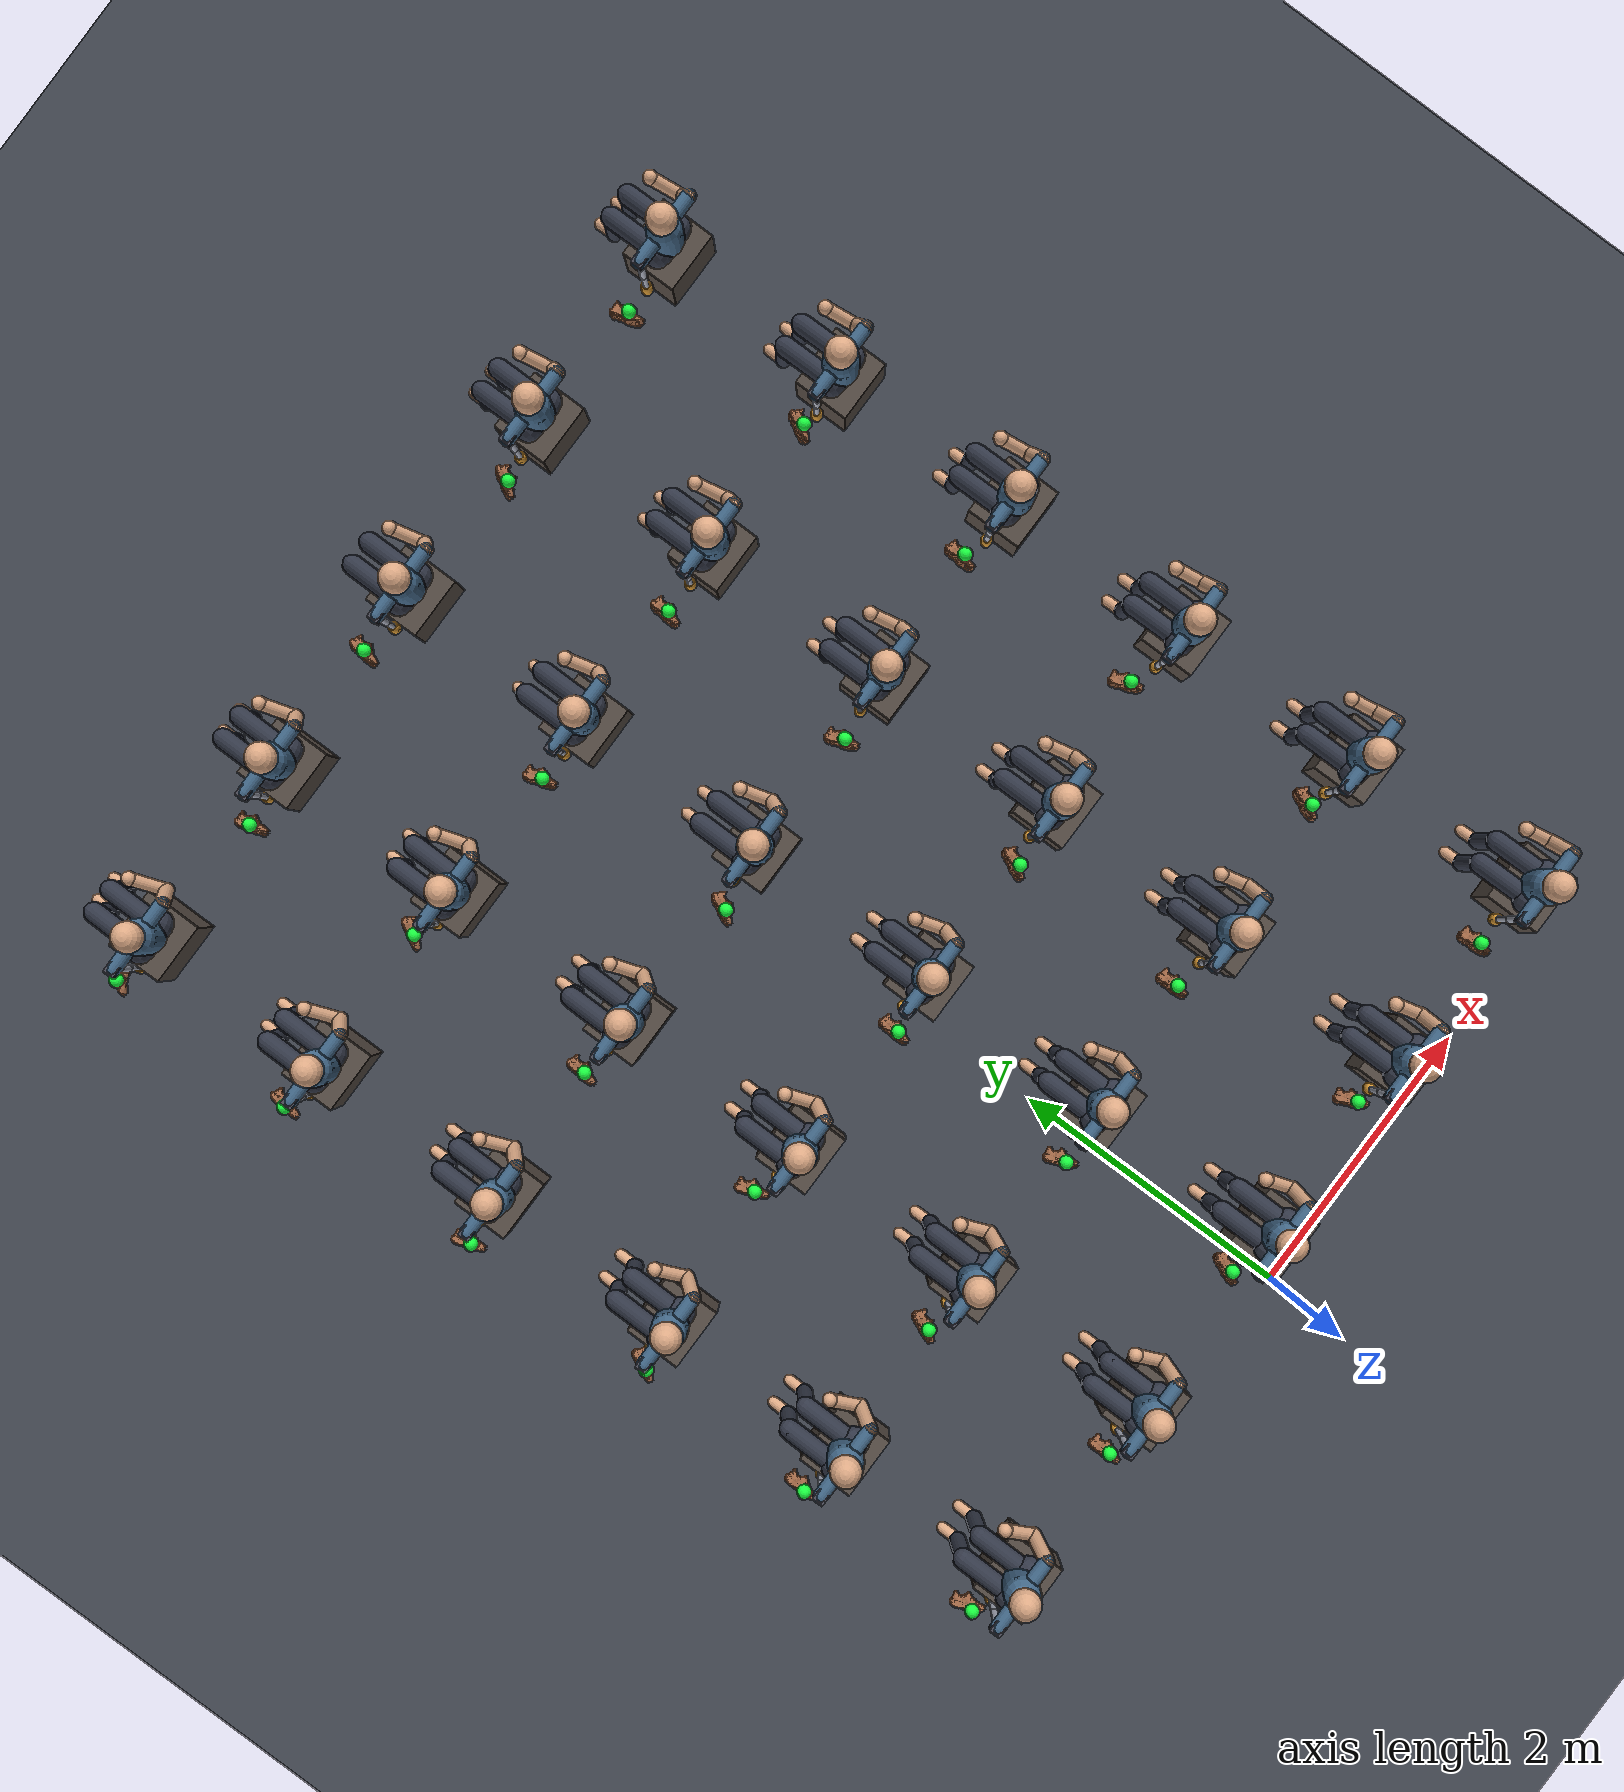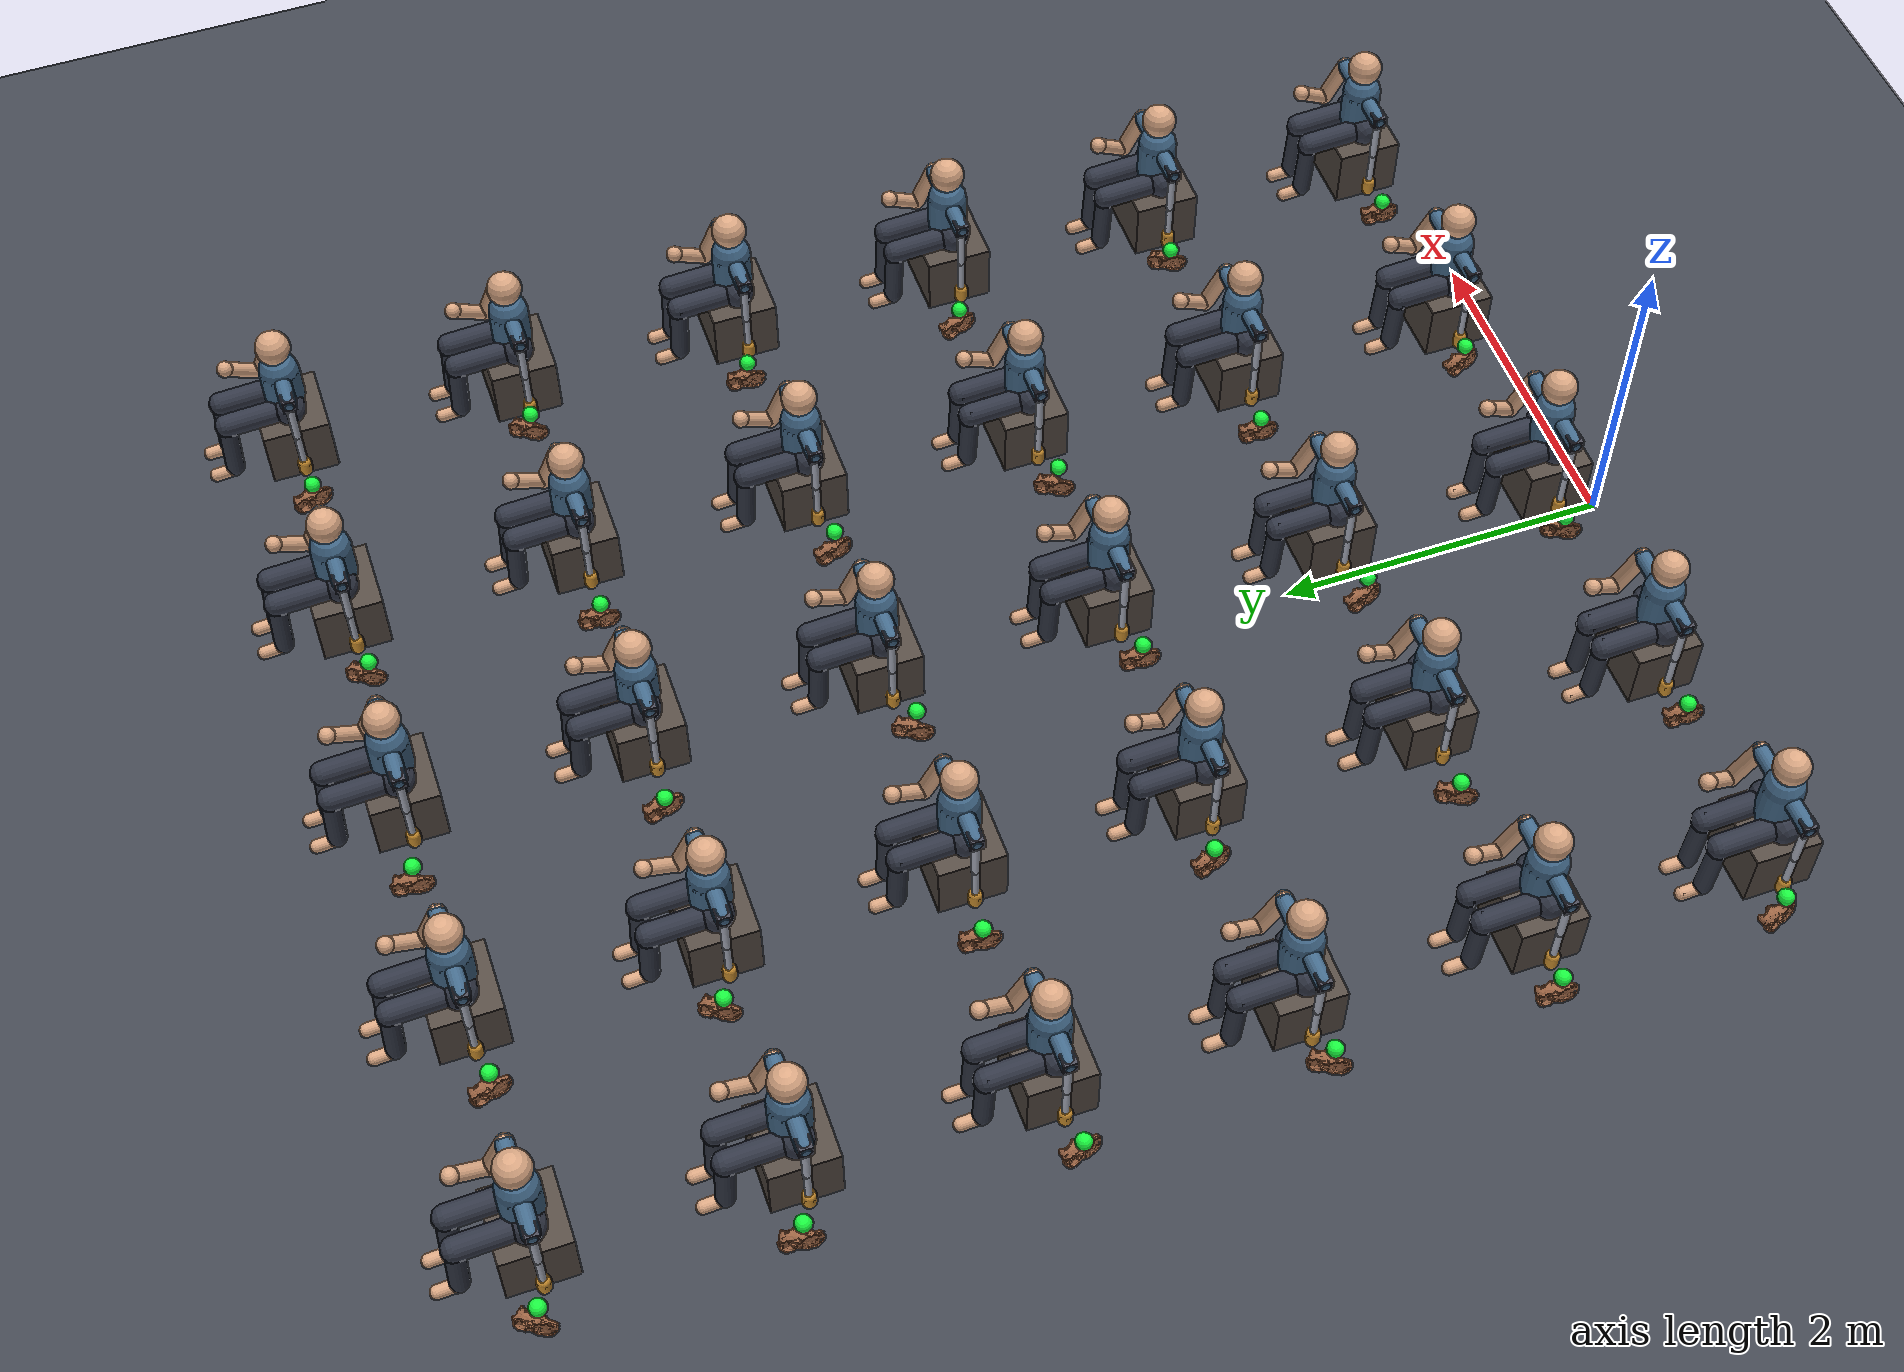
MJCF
<mujoco model="fleet">
  <compiler angle="radian" autolimits="true" meshdir="."/>
  <option gravity="0 0 -9.81" integrator="implicitfast" timestep="0.002"/>
  <visual>
    <global offwidth="1280" offheight="720"/>
    <headlight ambient="0.4 0.4 0.4" diffuse="0.6 0.6 0.6"/>
    <rgba haze="0.85 0.88 0.92 1"/>
  </visual>
  <asset>
    <texture name="skybox" type="skybox" builtin="gradient"
             rgb1="0.55 0.62 0.72" rgb2="0.10 0.12 0.16" width="512" height="512"/>
    <texture name="grid" type="2d" builtin="checker" rgb1="0.30 0.32 0.36"
             rgb2="0.22 0.24 0.28" width="512" height="512"/>
    <material name="grid" texture="grid" texrepeat="40 40" reflectance="0.05"/>
    <mesh name="upper_arm_mesh" file="arm_links/upper_arm.stl"/>
    <mesh name="forearm_mesh" file="arm_links/forearm.stl"/>
    <mesh name="gripper_mesh" file="arm_links/gripper.stl"/>
    <mesh name="shoe_mesh" file="arm_links/shoe.stl"/>
  </asset>
  <worldbody>
    <light pos="0 0 5" dir="0 0 -1" diffuse="0.9 0.9 0.9"/>
    <geom name="floor" type="plane" size="0 0 0.05" material="grid"/>
    <body name="c0_mount" pos="-2.8 7.25 0.7">
      <geom name="c0_mount_geom" type="box" size="0.04 0.04 0.04" rgba="0.3 0.3 0.35 1"/>
      <body name="c0_upper_arm" pos="0 0 0">
        <joint name="c0_shoulder_flex" type="hinge" axis="0 1 0" range="-1.5708 2.0944" damping="0.5" armature="0.01"/>
        <joint name="c0_shoulder_abduct" type="hinge" axis="1 0 0" range="-1.0472 1.5708" damping="0.5" armature="0.01"/>
        <geom name="c0_upper_arm_geom" type="mesh" mesh="upper_arm_mesh" rgba="0.7 0.72 0.78 1"/>
        <body name="c0_forearm" pos="0 0 -0.3">
        <joint name="c0_elbow" type="hinge" axis="0 1 0" range="0 2.2689" damping="0.5" armature="0.01"/>
        <geom name="c0_forearm_geom" type="mesh" mesh="forearm_mesh" rgba="0.7 0.72 0.78 1"/>
        <body name="c0_gripper" pos="0 0 -0.26">
        <joint name="c0_wrist" type="hinge" axis="1 0 0" range="-1.0472 1.0472" damping="0.5" armature="0.01"/>
        <geom name="c0_gripper_geom" type="mesh" mesh="gripper_mesh" rgba="0.85 0.6 0.2 1"/>
        <site name="c0_ee" pos="0 0 -0.06" size="0.012" rgba="0.95 0.2 0.2 1" group="3"/>
      </body>
      </body>
      </body>
    </body>
    <body name="c0_human" pos="0 0 0">
      <geom type="capsule" fromto="-2.8 7.25 0.7 -2.28 7.25 0.7" size="0.05" rgba="0.27 0.42 0.55 1" contype="0" conaffinity="0" group="2"/>
      <geom type="capsule" fromto="-2.54 7.25 0.49 -2.54 7.25 0.71" size="0.12" rgba="0.27 0.42 0.55 1" contype="0" conaffinity="0" group="2"/>
      <geom type="capsule" fromto="-2.54 7.25 0.72 -2.54 7.25 0.79" size="0.045" rgba="0.86 0.66 0.52 1" contype="0" conaffinity="0" group="2"/>
      <geom type="sphere" pos="-2.54 7.25 0.91" size="0.105" rgba="0.86 0.66 0.52 1" contype="0" conaffinity="0" group="2"/>
      <geom type="capsule" fromto="-2.28 7.25 0.7 -2.24 7.35 0.42" size="0.05" rgba="0.86 0.66 0.52 1" contype="0" conaffinity="0" group="2"/>
      <geom type="capsule" fromto="-2.24 7.35 0.42 -2.3 7.55 0.57" size="0.045" rgba="0.86 0.66 0.52 1" contype="0" conaffinity="0" group="2"/>
      <geom type="sphere" pos="-2.3 7.55 0.57" size="0.05" rgba="0.86 0.66 0.52 1" contype="0" conaffinity="0" group="2"/>
      <geom type="capsule" fromto="-2.64 7.25 0.47 -2.44 7.25 0.47" size="0.1" rgba="0.20 0.22 0.28 1" contype="0" conaffinity="0" group="2"/>
      <geom type="capsule" fromto="-2.63 7.25 0.47 -2.63 7.63 0.45" size="0.07" rgba="0.20 0.22 0.28 1" contype="0" conaffinity="0" group="2"/>
      <geom type="capsule" fromto="-2.45 7.25 0.47 -2.45 7.63 0.45" size="0.07" rgba="0.20 0.22 0.28 1" contype="0" conaffinity="0" group="2"/>
      <geom type="capsule" fromto="-2.63 7.63 0.45 -2.63 7.65 0.07" size="0.055" rgba="0.20 0.22 0.28 1" contype="0" conaffinity="0" group="2"/>
      <geom type="capsule" fromto="-2.45 7.63 0.45 -2.45 7.65 0.07" size="0.055" rgba="0.20 0.22 0.28 1" contype="0" conaffinity="0" group="2"/>
      <geom type="capsule" fromto="-2.63 7.65 0.05 -2.63 7.77 0.04" size="0.04" rgba="0.86 0.66 0.52 1" contype="0" conaffinity="0" group="2"/>
      <geom type="capsule" fromto="-2.45 7.65 0.05 -2.45 7.77 0.04" size="0.04" rgba="0.86 0.66 0.52 1" contype="0" conaffinity="0" group="2"/>
      <geom type="box" pos="-2.54 7.25 0.19" size="0.22 0.2 0.19" rgba="0.34 0.30 0.27 1" contype="0" conaffinity="0" group="2"/>
    </body>
    <body name="c0_shoe" pos="-2.9525 7.3336 0.005" euler="0 0 -0.6109"><geom type="mesh" mesh="shoe_mesh" rgba="0.62 0.4 0.27 1" contype="0" conaffinity="0" group="2"/></body>
    <body name="c0_target" pos="-2.9525 7.3136 0.19533"><geom type="sphere" size="0.05" rgba="0.1 1 0.25 1" contype="0" conaffinity="0" group="0"/></body>
    <body name="c1_mount" pos="-1.4 7.25 0.7">
      <geom name="c1_mount_geom" type="box" size="0.04 0.04 0.04" rgba="0.3 0.3 0.35 1"/>
      <body name="c1_upper_arm" pos="0 0 0">
        <joint name="c1_shoulder_flex" type="hinge" axis="0 1 0" range="-1.5708 2.0944" damping="0.5" armature="0.01"/>
        <joint name="c1_shoulder_abduct" type="hinge" axis="1 0 0" range="-1.0472 1.5708" damping="0.5" armature="0.01"/>
        <geom name="c1_upper_arm_geom" type="mesh" mesh="upper_arm_mesh" rgba="0.7 0.72 0.78 1"/>
        <body name="c1_forearm" pos="0 0 -0.3">
        <joint name="c1_elbow" type="hinge" axis="0 1 0" range="0 2.2689" damping="0.5" armature="0.01"/>
        <geom name="c1_forearm_geom" type="mesh" mesh="forearm_mesh" rgba="0.7 0.72 0.78 1"/>
        <body name="c1_gripper" pos="0 0 -0.26">
        <joint name="c1_wrist" type="hinge" axis="1 0 0" range="-1.0472 1.0472" damping="0.5" armature="0.01"/>
        <geom name="c1_gripper_geom" type="mesh" mesh="gripper_mesh" rgba="0.85 0.6 0.2 1"/>
        <site name="c1_ee" pos="0 0 -0.06" size="0.012" rgba="0.95 0.2 0.2 1" group="3"/>
      </body>
      </body>
      </body>
    </body>
    <body name="c1_human" pos="0 0 0">
      <geom type="capsule" fromto="-1.4 7.25 0.7 -0.88 7.25 0.7" size="0.05" rgba="0.27 0.42 0.55 1" contype="0" conaffinity="0" group="2"/>
      <geom type="capsule" fromto="-1.14 7.25 0.49 -1.14 7.25 0.71" size="0.12" rgba="0.27 0.42 0.55 1" contype="0" conaffinity="0" group="2"/>
      <geom type="capsule" fromto="-1.14 7.25 0.72 -1.14 7.25 0.79" size="0.045" rgba="0.86 0.66 0.52 1" contype="0" conaffinity="0" group="2"/>
      <geom type="sphere" pos="-1.14 7.25 0.91" size="0.105" rgba="0.86 0.66 0.52 1" contype="0" conaffinity="0" group="2"/>
      <geom type="capsule" fromto="-0.88 7.25 0.7 -0.84 7.35 0.42" size="0.05" rgba="0.86 0.66 0.52 1" contype="0" conaffinity="0" group="2"/>
      <geom type="capsule" fromto="-0.84 7.35 0.42 -0.9 7.55 0.57" size="0.045" rgba="0.86 0.66 0.52 1" contype="0" conaffinity="0" group="2"/>
      <geom type="sphere" pos="-0.9 7.55 0.57" size="0.05" rgba="0.86 0.66 0.52 1" contype="0" conaffinity="0" group="2"/>
      <geom type="capsule" fromto="-1.24 7.25 0.47 -1.04 7.25 0.47" size="0.1" rgba="0.20 0.22 0.28 1" contype="0" conaffinity="0" group="2"/>
      <geom type="capsule" fromto="-1.23 7.25 0.47 -1.23 7.63 0.45" size="0.07" rgba="0.20 0.22 0.28 1" contype="0" conaffinity="0" group="2"/>
      <geom type="capsule" fromto="-1.05 7.25 0.47 -1.05 7.63 0.45" size="0.07" rgba="0.20 0.22 0.28 1" contype="0" conaffinity="0" group="2"/>
      <geom type="capsule" fromto="-1.23 7.63 0.45 -1.23 7.65 0.07" size="0.055" rgba="0.20 0.22 0.28 1" contype="0" conaffinity="0" group="2"/>
      <geom type="capsule" fromto="-1.05 7.63 0.45 -1.05 7.65 0.07" size="0.055" rgba="0.20 0.22 0.28 1" contype="0" conaffinity="0" group="2"/>
      <geom type="capsule" fromto="-1.23 7.65 0.05 -1.23 7.77 0.04" size="0.04" rgba="0.86 0.66 0.52 1" contype="0" conaffinity="0" group="2"/>
      <geom type="capsule" fromto="-1.05 7.65 0.05 -1.05 7.77 0.04" size="0.04" rgba="0.86 0.66 0.52 1" contype="0" conaffinity="0" group="2"/>
      <geom type="box" pos="-1.14 7.25 0.19" size="0.22 0.2 0.19" rgba="0.34 0.30 0.27 1" contype="0" conaffinity="0" group="2"/>
    </body>
    <body name="c1_shoe" pos="-1.6085 7.238 0.005" euler="0 0 0.2094"><geom type="mesh" mesh="shoe_mesh" rgba="0.62 0.4 0.27 1" contype="0" conaffinity="0" group="2"/></body>
    <body name="c1_target" pos="-1.6085 7.218 0.20609"><geom type="sphere" size="0.05" rgba="0.1 1 0.25 1" contype="0" conaffinity="0" group="0"/></body>
    <body name="c2_mount" pos="0 7.25 0.7">
      <geom name="c2_mount_geom" type="box" size="0.04 0.04 0.04" rgba="0.3 0.3 0.35 1"/>
      <body name="c2_upper_arm" pos="0 0 0">
        <joint name="c2_shoulder_flex" type="hinge" axis="0 1 0" range="-1.5708 2.0944" damping="0.5" armature="0.01"/>
        <joint name="c2_shoulder_abduct" type="hinge" axis="1 0 0" range="-1.0472 1.5708" damping="0.5" armature="0.01"/>
        <geom name="c2_upper_arm_geom" type="mesh" mesh="upper_arm_mesh" rgba="0.7 0.72 0.78 1"/>
        <body name="c2_forearm" pos="0 0 -0.3">
        <joint name="c2_elbow" type="hinge" axis="0 1 0" range="0 2.2689" damping="0.5" armature="0.01"/>
        <geom name="c2_forearm_geom" type="mesh" mesh="forearm_mesh" rgba="0.7 0.72 0.78 1"/>
        <body name="c2_gripper" pos="0 0 -0.26">
        <joint name="c2_wrist" type="hinge" axis="1 0 0" range="-1.0472 1.0472" damping="0.5" armature="0.01"/>
        <geom name="c2_gripper_geom" type="mesh" mesh="gripper_mesh" rgba="0.85 0.6 0.2 1"/>
        <site name="c2_ee" pos="0 0 -0.06" size="0.012" rgba="0.95 0.2 0.2 1" group="3"/>
      </body>
      </body>
      </body>
    </body>
    <body name="c2_human" pos="0 0 0">
      <geom type="capsule" fromto="0 7.25 0.7 0.52 7.25 0.7" size="0.05" rgba="0.27 0.42 0.55 1" contype="0" conaffinity="0" group="2"/>
      <geom type="capsule" fromto="0.26 7.25 0.49 0.26 7.25 0.71" size="0.12" rgba="0.27 0.42 0.55 1" contype="0" conaffinity="0" group="2"/>
      <geom type="capsule" fromto="0.26 7.25 0.72 0.26 7.25 0.79" size="0.045" rgba="0.86 0.66 0.52 1" contype="0" conaffinity="0" group="2"/>
      <geom type="sphere" pos="0.26 7.25 0.91" size="0.105" rgba="0.86 0.66 0.52 1" contype="0" conaffinity="0" group="2"/>
      <geom type="capsule" fromto="0.52 7.25 0.7 0.56 7.35 0.42" size="0.05" rgba="0.86 0.66 0.52 1" contype="0" conaffinity="0" group="2"/>
      <geom type="capsule" fromto="0.56 7.35 0.42 0.5 7.55 0.57" size="0.045" rgba="0.86 0.66 0.52 1" contype="0" conaffinity="0" group="2"/>
      <geom type="sphere" pos="0.5 7.55 0.57" size="0.05" rgba="0.86 0.66 0.52 1" contype="0" conaffinity="0" group="2"/>
      <geom type="capsule" fromto="0.16 7.25 0.47 0.36 7.25 0.47" size="0.1" rgba="0.20 0.22 0.28 1" contype="0" conaffinity="0" group="2"/>
      <geom type="capsule" fromto="0.17 7.25 0.47 0.17 7.63 0.45" size="0.07" rgba="0.20 0.22 0.28 1" contype="0" conaffinity="0" group="2"/>
      <geom type="capsule" fromto="0.35 7.25 0.47 0.35 7.63 0.45" size="0.07" rgba="0.20 0.22 0.28 1" contype="0" conaffinity="0" group="2"/>
      <geom type="capsule" fromto="0.17 7.63 0.45 0.17 7.65 0.07" size="0.055" rgba="0.20 0.22 0.28 1" contype="0" conaffinity="0" group="2"/>
      <geom type="capsule" fromto="0.35 7.63 0.45 0.35 7.65 0.07" size="0.055" rgba="0.20 0.22 0.28 1" contype="0" conaffinity="0" group="2"/>
      <geom type="capsule" fromto="0.17 7.65 0.05 0.17 7.77 0.04" size="0.04" rgba="0.86 0.66 0.52 1" contype="0" conaffinity="0" group="2"/>
      <geom type="capsule" fromto="0.35 7.65 0.05 0.35 7.77 0.04" size="0.04" rgba="0.86 0.66 0.52 1" contype="0" conaffinity="0" group="2"/>
      <geom type="box" pos="0.26 7.25 0.19" size="0.22 0.2 0.19" rgba="0.34 0.30 0.27 1" contype="0" conaffinity="0" group="2"/>
    </body>
    <body name="c2_shoe" pos="-0.23926 7.3214 0.005" euler="0 0 -0.192"><geom type="mesh" mesh="shoe_mesh" rgba="0.62 0.4 0.27 1" contype="0" conaffinity="0" group="2"/></body>
    <body name="c2_target" pos="-0.23926 7.3014 0.19768"><geom type="sphere" size="0.05" rgba="0.1 1 0.25 1" contype="0" conaffinity="0" group="0"/></body>
    <body name="c3_mount" pos="1.4 7.25 0.7">
      <geom name="c3_mount_geom" type="box" size="0.04 0.04 0.04" rgba="0.3 0.3 0.35 1"/>
      <body name="c3_upper_arm" pos="0 0 0">
        <joint name="c3_shoulder_flex" type="hinge" axis="0 1 0" range="-1.5708 2.0944" damping="0.5" armature="0.01"/>
        <joint name="c3_shoulder_abduct" type="hinge" axis="1 0 0" range="-1.0472 1.5708" damping="0.5" armature="0.01"/>
        <geom name="c3_upper_arm_geom" type="mesh" mesh="upper_arm_mesh" rgba="0.7 0.72 0.78 1"/>
        <body name="c3_forearm" pos="0 0 -0.3">
        <joint name="c3_elbow" type="hinge" axis="0 1 0" range="0 2.2689" damping="0.5" armature="0.01"/>
        <geom name="c3_forearm_geom" type="mesh" mesh="forearm_mesh" rgba="0.7 0.72 0.78 1"/>
        <body name="c3_gripper" pos="0 0 -0.26">
        <joint name="c3_wrist" type="hinge" axis="1 0 0" range="-1.0472 1.0472" damping="0.5" armature="0.01"/>
        <geom name="c3_gripper_geom" type="mesh" mesh="gripper_mesh" rgba="0.85 0.6 0.2 1"/>
        <site name="c3_ee" pos="0 0 -0.06" size="0.012" rgba="0.95 0.2 0.2 1" group="3"/>
      </body>
      </body>
      </body>
    </body>
    <body name="c3_human" pos="0 0 0">
      <geom type="capsule" fromto="1.4 7.25 0.7 1.92 7.25 0.7" size="0.05" rgba="0.27 0.42 0.55 1" contype="0" conaffinity="0" group="2"/>
      <geom type="capsule" fromto="1.66 7.25 0.49 1.66 7.25 0.71" size="0.12" rgba="0.27 0.42 0.55 1" contype="0" conaffinity="0" group="2"/>
      <geom type="capsule" fromto="1.66 7.25 0.72 1.66 7.25 0.79" size="0.045" rgba="0.86 0.66 0.52 1" contype="0" conaffinity="0" group="2"/>
      <geom type="sphere" pos="1.66 7.25 0.91" size="0.105" rgba="0.86 0.66 0.52 1" contype="0" conaffinity="0" group="2"/>
      <geom type="capsule" fromto="1.92 7.25 0.7 1.96 7.35 0.42" size="0.05" rgba="0.86 0.66 0.52 1" contype="0" conaffinity="0" group="2"/>
      <geom type="capsule" fromto="1.96 7.35 0.42 1.9 7.55 0.57" size="0.045" rgba="0.86 0.66 0.52 1" contype="0" conaffinity="0" group="2"/>
      <geom type="sphere" pos="1.9 7.55 0.57" size="0.05" rgba="0.86 0.66 0.52 1" contype="0" conaffinity="0" group="2"/>
      <geom type="capsule" fromto="1.56 7.25 0.47 1.76 7.25 0.47" size="0.1" rgba="0.20 0.22 0.28 1" contype="0" conaffinity="0" group="2"/>
      <geom type="capsule" fromto="1.57 7.25 0.47 1.57 7.63 0.45" size="0.07" rgba="0.20 0.22 0.28 1" contype="0" conaffinity="0" group="2"/>
      <geom type="capsule" fromto="1.75 7.25 0.47 1.75 7.63 0.45" size="0.07" rgba="0.20 0.22 0.28 1" contype="0" conaffinity="0" group="2"/>
      <geom type="capsule" fromto="1.57 7.63 0.45 1.57 7.65 0.07" size="0.055" rgba="0.20 0.22 0.28 1" contype="0" conaffinity="0" group="2"/>
      <geom type="capsule" fromto="1.75 7.63 0.45 1.75 7.65 0.07" size="0.055" rgba="0.20 0.22 0.28 1" contype="0" conaffinity="0" group="2"/>
      <geom type="capsule" fromto="1.57 7.65 0.05 1.57 7.77 0.04" size="0.04" rgba="0.86 0.66 0.52 1" contype="0" conaffinity="0" group="2"/>
      <geom type="capsule" fromto="1.75 7.65 0.05 1.75 7.77 0.04" size="0.04" rgba="0.86 0.66 0.52 1" contype="0" conaffinity="0" group="2"/>
      <geom type="box" pos="1.66 7.25 0.19" size="0.22 0.2 0.19" rgba="0.34 0.30 0.27 1" contype="0" conaffinity="0" group="2"/>
    </body>
    <body name="c3_shoe" pos="1.2255 7.2385 0.005" euler="0 0 -0.5934"><geom type="mesh" mesh="shoe_mesh" rgba="0.62 0.4 0.27 1" contype="0" conaffinity="0" group="2"/></body>
    <body name="c3_target" pos="1.2255 7.2185 0.14063"><geom type="sphere" size="0.05" rgba="0.1 1 0.25 1" contype="0" conaffinity="0" group="0"/></body>
    <body name="c4_mount" pos="2.8 7.25 0.7">
      <geom name="c4_mount_geom" type="box" size="0.04 0.04 0.04" rgba="0.3 0.3 0.35 1"/>
      <body name="c4_upper_arm" pos="0 0 0">
        <joint name="c4_shoulder_flex" type="hinge" axis="0 1 0" range="-1.5708 2.0944" damping="0.5" armature="0.01"/>
        <joint name="c4_shoulder_abduct" type="hinge" axis="1 0 0" range="-1.0472 1.5708" damping="0.5" armature="0.01"/>
        <geom name="c4_upper_arm_geom" type="mesh" mesh="upper_arm_mesh" rgba="0.7 0.72 0.78 1"/>
        <body name="c4_forearm" pos="0 0 -0.3">
        <joint name="c4_elbow" type="hinge" axis="0 1 0" range="0 2.2689" damping="0.5" armature="0.01"/>
        <geom name="c4_forearm_geom" type="mesh" mesh="forearm_mesh" rgba="0.7 0.72 0.78 1"/>
        <body name="c4_gripper" pos="0 0 -0.26">
        <joint name="c4_wrist" type="hinge" axis="1 0 0" range="-1.0472 1.0472" damping="0.5" armature="0.01"/>
        <geom name="c4_gripper_geom" type="mesh" mesh="gripper_mesh" rgba="0.85 0.6 0.2 1"/>
        <site name="c4_ee" pos="0 0 -0.06" size="0.012" rgba="0.95 0.2 0.2 1" group="3"/>
      </body>
      </body>
      </body>
    </body>
    <body name="c4_human" pos="0 0 0">
      <geom type="capsule" fromto="2.8 7.25 0.7 3.32 7.25 0.7" size="0.05" rgba="0.27 0.42 0.55 1" contype="0" conaffinity="0" group="2"/>
      <geom type="capsule" fromto="3.06 7.25 0.49 3.06 7.25 0.71" size="0.12" rgba="0.27 0.42 0.55 1" contype="0" conaffinity="0" group="2"/>
      <geom type="capsule" fromto="3.06 7.25 0.72 3.06 7.25 0.79" size="0.045" rgba="0.86 0.66 0.52 1" contype="0" conaffinity="0" group="2"/>
      <geom type="sphere" pos="3.06 7.25 0.91" size="0.105" rgba="0.86 0.66 0.52 1" contype="0" conaffinity="0" group="2"/>
      <geom type="capsule" fromto="3.32 7.25 0.7 3.36 7.35 0.42" size="0.05" rgba="0.86 0.66 0.52 1" contype="0" conaffinity="0" group="2"/>
      <geom type="capsule" fromto="3.36 7.35 0.42 3.3 7.55 0.57" size="0.045" rgba="0.86 0.66 0.52 1" contype="0" conaffinity="0" group="2"/>
      <geom type="sphere" pos="3.3 7.55 0.57" size="0.05" rgba="0.86 0.66 0.52 1" contype="0" conaffinity="0" group="2"/>
      <geom type="capsule" fromto="2.96 7.25 0.47 3.16 7.25 0.47" size="0.1" rgba="0.20 0.22 0.28 1" contype="0" conaffinity="0" group="2"/>
      <geom type="capsule" fromto="2.97 7.25 0.47 2.97 7.63 0.45" size="0.07" rgba="0.20 0.22 0.28 1" contype="0" conaffinity="0" group="2"/>
      <geom type="capsule" fromto="3.15 7.25 0.47 3.15 7.63 0.45" size="0.07" rgba="0.20 0.22 0.28 1" contype="0" conaffinity="0" group="2"/>
      <geom type="capsule" fromto="2.97 7.63 0.45 2.97 7.65 0.07" size="0.055" rgba="0.20 0.22 0.28 1" contype="0" conaffinity="0" group="2"/>
      <geom type="capsule" fromto="3.15 7.63 0.45 3.15 7.65 0.07" size="0.055" rgba="0.20 0.22 0.28 1" contype="0" conaffinity="0" group="2"/>
      <geom type="capsule" fromto="2.97 7.65 0.05 2.97 7.77 0.04" size="0.04" rgba="0.86 0.66 0.52 1" contype="0" conaffinity="0" group="2"/>
      <geom type="capsule" fromto="3.15 7.65 0.05 3.15 7.77 0.04" size="0.04" rgba="0.86 0.66 0.52 1" contype="0" conaffinity="0" group="2"/>
      <geom type="box" pos="3.06 7.25 0.19" size="0.22 0.2 0.19" rgba="0.34 0.30 0.27 1" contype="0" conaffinity="0" group="2"/>
    </body>
    <body name="c4_shoe" pos="2.5957 7.2612 0.005" euler="0 0 0.2269"><geom type="mesh" mesh="shoe_mesh" rgba="0.62 0.4 0.27 1" contype="0" conaffinity="0" group="2"/></body>
    <body name="c4_target" pos="2.5957 7.2412 0.1655"><geom type="sphere" size="0.05" rgba="0.1 1 0.25 1" contype="0" conaffinity="0" group="0"/></body>
    <body name="c5_mount" pos="-2.8 5.85 0.7">
      <geom name="c5_mount_geom" type="box" size="0.04 0.04 0.04" rgba="0.3 0.3 0.35 1"/>
      <body name="c5_upper_arm" pos="0 0 0">
        <joint name="c5_shoulder_flex" type="hinge" axis="0 1 0" range="-1.5708 2.0944" damping="0.5" armature="0.01"/>
        <joint name="c5_shoulder_abduct" type="hinge" axis="1 0 0" range="-1.0472 1.5708" damping="0.5" armature="0.01"/>
        <geom name="c5_upper_arm_geom" type="mesh" mesh="upper_arm_mesh" rgba="0.7 0.72 0.78 1"/>
        <body name="c5_forearm" pos="0 0 -0.3">
        <joint name="c5_elbow" type="hinge" axis="0 1 0" range="0 2.2689" damping="0.5" armature="0.01"/>
        <geom name="c5_forearm_geom" type="mesh" mesh="forearm_mesh" rgba="0.7 0.72 0.78 1"/>
        <body name="c5_gripper" pos="0 0 -0.26">
        <joint name="c5_wrist" type="hinge" axis="1 0 0" range="-1.0472 1.0472" damping="0.5" armature="0.01"/>
        <geom name="c5_gripper_geom" type="mesh" mesh="gripper_mesh" rgba="0.85 0.6 0.2 1"/>
        <site name="c5_ee" pos="0 0 -0.06" size="0.012" rgba="0.95 0.2 0.2 1" group="3"/>
      </body>
      </body>
      </body>
    </body>
    <body name="c5_human" pos="0 0 0">
      <geom type="capsule" fromto="-2.8 5.85 0.7 -2.28 5.85 0.7" size="0.05" rgba="0.27 0.42 0.55 1" contype="0" conaffinity="0" group="2"/>
      <geom type="capsule" fromto="-2.54 5.85 0.49 -2.54 5.85 0.71" size="0.12" rgba="0.27 0.42 0.55 1" contype="0" conaffinity="0" group="2"/>
      <geom type="capsule" fromto="-2.54 5.85 0.72 -2.54 5.85 0.79" size="0.045" rgba="0.86 0.66 0.52 1" contype="0" conaffinity="0" group="2"/>
      <geom type="sphere" pos="-2.54 5.85 0.91" size="0.105" rgba="0.86 0.66 0.52 1" contype="0" conaffinity="0" group="2"/>
      <geom type="capsule" fromto="-2.28 5.85 0.7 -2.24 5.95 0.42" size="0.05" rgba="0.86 0.66 0.52 1" contype="0" conaffinity="0" group="2"/>
      <geom type="capsule" fromto="-2.24 5.95 0.42 -2.3 6.15 0.57" size="0.045" rgba="0.86 0.66 0.52 1" contype="0" conaffinity="0" group="2"/>
      <geom type="sphere" pos="-2.3 6.15 0.57" size="0.05" rgba="0.86 0.66 0.52 1" contype="0" conaffinity="0" group="2"/>
      <geom type="capsule" fromto="-2.64 5.85 0.47 -2.44 5.85 0.47" size="0.1" rgba="0.20 0.22 0.28 1" contype="0" conaffinity="0" group="2"/>
      <geom type="capsule" fromto="-2.63 5.85 0.47 -2.63 6.23 0.45" size="0.07" rgba="0.20 0.22 0.28 1" contype="0" conaffinity="0" group="2"/>
      <geom type="capsule" fromto="-2.45 5.85 0.47 -2.45 6.23 0.45" size="0.07" rgba="0.20 0.22 0.28 1" contype="0" conaffinity="0" group="2"/>
      <geom type="capsule" fromto="-2.63 6.23 0.45 -2.63 6.25 0.07" size="0.055" rgba="0.20 0.22 0.28 1" contype="0" conaffinity="0" group="2"/>
      <geom type="capsule" fromto="-2.45 6.23 0.45 -2.45 6.25 0.07" size="0.055" rgba="0.20 0.22 0.28 1" contype="0" conaffinity="0" group="2"/>
      <geom type="capsule" fromto="-2.63 6.25 0.05 -2.63 6.37 0.04" size="0.04" rgba="0.86 0.66 0.52 1" contype="0" conaffinity="0" group="2"/>
      <geom type="capsule" fromto="-2.45 6.25 0.05 -2.45 6.37 0.04" size="0.04" rgba="0.86 0.66 0.52 1" contype="0" conaffinity="0" group="2"/>
      <geom type="box" pos="-2.54 5.85 0.19" size="0.22 0.2 0.19" rgba="0.34 0.30 0.27 1" contype="0" conaffinity="0" group="2"/>
    </body>
    <body name="c5_shoe" pos="-2.9625 5.9493 0.005" euler="0 0 -0.1745"><geom type="mesh" mesh="shoe_mesh" rgba="0.62 0.4 0.27 1" contype="0" conaffinity="0" group="2"/></body>
    <body name="c5_target" pos="-2.9625 5.9293 0.19719"><geom type="sphere" size="0.05" rgba="0.1 1 0.25 1" contype="0" conaffinity="0" group="0"/></body>
    <body name="c6_mount" pos="-1.4 5.85 0.7">
      <geom name="c6_mount_geom" type="box" size="0.04 0.04 0.04" rgba="0.3 0.3 0.35 1"/>
      <body name="c6_upper_arm" pos="0 0 0">
        <joint name="c6_shoulder_flex" type="hinge" axis="0 1 0" range="-1.5708 2.0944" damping="0.5" armature="0.01"/>
        <joint name="c6_shoulder_abduct" type="hinge" axis="1 0 0" range="-1.0472 1.5708" damping="0.5" armature="0.01"/>
        <geom name="c6_upper_arm_geom" type="mesh" mesh="upper_arm_mesh" rgba="0.7 0.72 0.78 1"/>
        <body name="c6_forearm" pos="0 0 -0.3">
        <joint name="c6_elbow" type="hinge" axis="0 1 0" range="0 2.2689" damping="0.5" armature="0.01"/>
        <geom name="c6_forearm_geom" type="mesh" mesh="forearm_mesh" rgba="0.7 0.72 0.78 1"/>
        <body name="c6_gripper" pos="0 0 -0.26">
        <joint name="c6_wrist" type="hinge" axis="1 0 0" range="-1.0472 1.0472" damping="0.5" armature="0.01"/>
        <geom name="c6_gripper_geom" type="mesh" mesh="gripper_mesh" rgba="0.85 0.6 0.2 1"/>
        <site name="c6_ee" pos="0 0 -0.06" size="0.012" rgba="0.95 0.2 0.2 1" group="3"/>
      </body>
      </body>
      </body>
    </body>
    <body name="c6_human" pos="0 0 0">
      <geom type="capsule" fromto="-1.4 5.85 0.7 -0.88 5.85 0.7" size="0.05" rgba="0.27 0.42 0.55 1" contype="0" conaffinity="0" group="2"/>
      <geom type="capsule" fromto="-1.14 5.85 0.49 -1.14 5.85 0.71" size="0.12" rgba="0.27 0.42 0.55 1" contype="0" conaffinity="0" group="2"/>
      <geom type="capsule" fromto="-1.14 5.85 0.72 -1.14 5.85 0.79" size="0.045" rgba="0.86 0.66 0.52 1" contype="0" conaffinity="0" group="2"/>
      <geom type="sphere" pos="-1.14 5.85 0.91" size="0.105" rgba="0.86 0.66 0.52 1" contype="0" conaffinity="0" group="2"/>
      <geom type="capsule" fromto="-0.88 5.85 0.7 -0.84 5.95 0.42" size="0.05" rgba="0.86 0.66 0.52 1" contype="0" conaffinity="0" group="2"/>
      <geom type="capsule" fromto="-0.84 5.95 0.42 -0.9 6.15 0.57" size="0.045" rgba="0.86 0.66 0.52 1" contype="0" conaffinity="0" group="2"/>
      <geom type="sphere" pos="-0.9 6.15 0.57" size="0.05" rgba="0.86 0.66 0.52 1" contype="0" conaffinity="0" group="2"/>
      <geom type="capsule" fromto="-1.24 5.85 0.47 -1.04 5.85 0.47" size="0.1" rgba="0.20 0.22 0.28 1" contype="0" conaffinity="0" group="2"/>
      <geom type="capsule" fromto="-1.23 5.85 0.47 -1.23 6.23 0.45" size="0.07" rgba="0.20 0.22 0.28 1" contype="0" conaffinity="0" group="2"/>
      <geom type="capsule" fromto="-1.05 5.85 0.47 -1.05 6.23 0.45" size="0.07" rgba="0.20 0.22 0.28 1" contype="0" conaffinity="0" group="2"/>
      <geom type="capsule" fromto="-1.23 6.23 0.45 -1.23 6.25 0.07" size="0.055" rgba="0.20 0.22 0.28 1" contype="0" conaffinity="0" group="2"/>
      <geom type="capsule" fromto="-1.05 6.23 0.45 -1.05 6.25 0.07" size="0.055" rgba="0.20 0.22 0.28 1" contype="0" conaffinity="0" group="2"/>
      <geom type="capsule" fromto="-1.23 6.25 0.05 -1.23 6.37 0.04" size="0.04" rgba="0.86 0.66 0.52 1" contype="0" conaffinity="0" group="2"/>
      <geom type="capsule" fromto="-1.05 6.25 0.05 -1.05 6.37 0.04" size="0.04" rgba="0.86 0.66 0.52 1" contype="0" conaffinity="0" group="2"/>
      <geom type="box" pos="-1.14 5.85 0.19" size="0.22 0.2 0.19" rgba="0.34 0.30 0.27 1" contype="0" conaffinity="0" group="2"/>
    </body>
    <body name="c6_shoe" pos="-1.5529 5.9482 0.005" euler="0 0 -0.576"><geom type="mesh" mesh="shoe_mesh" rgba="0.62 0.4 0.27 1" contype="0" conaffinity="0" group="2"/></body>
    <body name="c6_target" pos="-1.5529 5.9282 0.13368"><geom type="sphere" size="0.05" rgba="0.1 1 0.25 1" contype="0" conaffinity="0" group="0"/></body>
    <body name="c7_mount" pos="0 5.85 0.7">
      <geom name="c7_mount_geom" type="box" size="0.04 0.04 0.04" rgba="0.3 0.3 0.35 1"/>
      <body name="c7_upper_arm" pos="0 0 0">
        <joint name="c7_shoulder_flex" type="hinge" axis="0 1 0" range="-1.5708 2.0944" damping="0.5" armature="0.01"/>
        <joint name="c7_shoulder_abduct" type="hinge" axis="1 0 0" range="-1.0472 1.5708" damping="0.5" armature="0.01"/>
        <geom name="c7_upper_arm_geom" type="mesh" mesh="upper_arm_mesh" rgba="0.7 0.72 0.78 1"/>
        <body name="c7_forearm" pos="0 0 -0.3">
        <joint name="c7_elbow" type="hinge" axis="0 1 0" range="0 2.2689" damping="0.5" armature="0.01"/>
        <geom name="c7_forearm_geom" type="mesh" mesh="forearm_mesh" rgba="0.7 0.72 0.78 1"/>
        <body name="c7_gripper" pos="0 0 -0.26">
        <joint name="c7_wrist" type="hinge" axis="1 0 0" range="-1.0472 1.0472" damping="0.5" armature="0.01"/>
        <geom name="c7_gripper_geom" type="mesh" mesh="gripper_mesh" rgba="0.85 0.6 0.2 1"/>
        <site name="c7_ee" pos="0 0 -0.06" size="0.012" rgba="0.95 0.2 0.2 1" group="3"/>
      </body>
      </body>
      </body>
    </body>
    <body name="c7_human" pos="0 0 0">
      <geom type="capsule" fromto="0 5.85 0.7 0.52 5.85 0.7" size="0.05" rgba="0.27 0.42 0.55 1" contype="0" conaffinity="0" group="2"/>
      <geom type="capsule" fromto="0.26 5.85 0.49 0.26 5.85 0.71" size="0.12" rgba="0.27 0.42 0.55 1" contype="0" conaffinity="0" group="2"/>
      <geom type="capsule" fromto="0.26 5.85 0.72 0.26 5.85 0.79" size="0.045" rgba="0.86 0.66 0.52 1" contype="0" conaffinity="0" group="2"/>
      <geom type="sphere" pos="0.26 5.85 0.91" size="0.105" rgba="0.86 0.66 0.52 1" contype="0" conaffinity="0" group="2"/>
      <geom type="capsule" fromto="0.52 5.85 0.7 0.56 5.95 0.42" size="0.05" rgba="0.86 0.66 0.52 1" contype="0" conaffinity="0" group="2"/>
      <geom type="capsule" fromto="0.56 5.95 0.42 0.5 6.15 0.57" size="0.045" rgba="0.86 0.66 0.52 1" contype="0" conaffinity="0" group="2"/>
      <geom type="sphere" pos="0.5 6.15 0.57" size="0.05" rgba="0.86 0.66 0.52 1" contype="0" conaffinity="0" group="2"/>
      <geom type="capsule" fromto="0.16 5.85 0.47 0.36 5.85 0.47" size="0.1" rgba="0.20 0.22 0.28 1" contype="0" conaffinity="0" group="2"/>
      <geom type="capsule" fromto="0.17 5.85 0.47 0.17 6.23 0.45" size="0.07" rgba="0.20 0.22 0.28 1" contype="0" conaffinity="0" group="2"/>
      <geom type="capsule" fromto="0.35 5.85 0.47 0.35 6.23 0.45" size="0.07" rgba="0.20 0.22 0.28 1" contype="0" conaffinity="0" group="2"/>
      <geom type="capsule" fromto="0.17 6.23 0.45 0.17 6.25 0.07" size="0.055" rgba="0.20 0.22 0.28 1" contype="0" conaffinity="0" group="2"/>
      <geom type="capsule" fromto="0.35 6.23 0.45 0.35 6.25 0.07" size="0.055" rgba="0.20 0.22 0.28 1" contype="0" conaffinity="0" group="2"/>
      <geom type="capsule" fromto="0.17 6.25 0.05 0.17 6.37 0.04" size="0.04" rgba="0.86 0.66 0.52 1" contype="0" conaffinity="0" group="2"/>
      <geom type="capsule" fromto="0.35 6.25 0.05 0.35 6.37 0.04" size="0.04" rgba="0.86 0.66 0.52 1" contype="0" conaffinity="0" group="2"/>
      <geom type="box" pos="0.26 5.85 0.19" size="0.22 0.2 0.19" rgba="0.34 0.30 0.27 1" contype="0" conaffinity="0" group="2"/>
    </body>
    <body name="c7_shoe" pos="-0.21757 5.888 0.005" euler="0 0 0.2443"><geom type="mesh" mesh="shoe_mesh" rgba="0.62 0.4 0.27 1" contype="0" conaffinity="0" group="2"/></body>
    <body name="c7_target" pos="-0.21757 5.868 0.11483"><geom type="sphere" size="0.05" rgba="0.1 1 0.25 1" contype="0" conaffinity="0" group="0"/></body>
    <body name="c8_mount" pos="1.4 5.85 0.7">
      <geom name="c8_mount_geom" type="box" size="0.04 0.04 0.04" rgba="0.3 0.3 0.35 1"/>
      <body name="c8_upper_arm" pos="0 0 0">
        <joint name="c8_shoulder_flex" type="hinge" axis="0 1 0" range="-1.5708 2.0944" damping="0.5" armature="0.01"/>
        <joint name="c8_shoulder_abduct" type="hinge" axis="1 0 0" range="-1.0472 1.5708" damping="0.5" armature="0.01"/>
        <geom name="c8_upper_arm_geom" type="mesh" mesh="upper_arm_mesh" rgba="0.7 0.72 0.78 1"/>
        <body name="c8_forearm" pos="0 0 -0.3">
        <joint name="c8_elbow" type="hinge" axis="0 1 0" range="0 2.2689" damping="0.5" armature="0.01"/>
        <geom name="c8_forearm_geom" type="mesh" mesh="forearm_mesh" rgba="0.7 0.72 0.78 1"/>
        <body name="c8_gripper" pos="0 0 -0.26">
        <joint name="c8_wrist" type="hinge" axis="1 0 0" range="-1.0472 1.0472" damping="0.5" armature="0.01"/>
        <geom name="c8_gripper_geom" type="mesh" mesh="gripper_mesh" rgba="0.85 0.6 0.2 1"/>
        <site name="c8_ee" pos="0 0 -0.06" size="0.012" rgba="0.95 0.2 0.2 1" group="3"/>
      </body>
      </body>
      </body>
    </body>
    <body name="c8_human" pos="0 0 0">
      <geom type="capsule" fromto="1.4 5.85 0.7 1.92 5.85 0.7" size="0.05" rgba="0.27 0.42 0.55 1" contype="0" conaffinity="0" group="2"/>
      <geom type="capsule" fromto="1.66 5.85 0.49 1.66 5.85 0.71" size="0.12" rgba="0.27 0.42 0.55 1" contype="0" conaffinity="0" group="2"/>
      <geom type="capsule" fromto="1.66 5.85 0.72 1.66 5.85 0.79" size="0.045" rgba="0.86 0.66 0.52 1" contype="0" conaffinity="0" group="2"/>
      <geom type="sphere" pos="1.66 5.85 0.91" size="0.105" rgba="0.86 0.66 0.52 1" contype="0" conaffinity="0" group="2"/>
      <geom type="capsule" fromto="1.92 5.85 0.7 1.96 5.95 0.42" size="0.05" rgba="0.86 0.66 0.52 1" contype="0" conaffinity="0" group="2"/>
      <geom type="capsule" fromto="1.96 5.95 0.42 1.9 6.15 0.57" size="0.045" rgba="0.86 0.66 0.52 1" contype="0" conaffinity="0" group="2"/>
      <geom type="sphere" pos="1.9 6.15 0.57" size="0.05" rgba="0.86 0.66 0.52 1" contype="0" conaffinity="0" group="2"/>
      <geom type="capsule" fromto="1.56 5.85 0.47 1.76 5.85 0.47" size="0.1" rgba="0.20 0.22 0.28 1" contype="0" conaffinity="0" group="2"/>
      <geom type="capsule" fromto="1.57 5.85 0.47 1.57 6.23 0.45" size="0.07" rgba="0.20 0.22 0.28 1" contype="0" conaffinity="0" group="2"/>
      <geom type="capsule" fromto="1.75 5.85 0.47 1.75 6.23 0.45" size="0.07" rgba="0.20 0.22 0.28 1" contype="0" conaffinity="0" group="2"/>
      <geom type="capsule" fromto="1.57 6.23 0.45 1.57 6.25 0.07" size="0.055" rgba="0.20 0.22 0.28 1" contype="0" conaffinity="0" group="2"/>
      <geom type="capsule" fromto="1.75 6.23 0.45 1.75 6.25 0.07" size="0.055" rgba="0.20 0.22 0.28 1" contype="0" conaffinity="0" group="2"/>
      <geom type="capsule" fromto="1.57 6.25 0.05 1.57 6.37 0.04" size="0.04" rgba="0.86 0.66 0.52 1" contype="0" conaffinity="0" group="2"/>
      <geom type="capsule" fromto="1.75 6.25 0.05 1.75 6.37 0.04" size="0.04" rgba="0.86 0.66 0.52 1" contype="0" conaffinity="0" group="2"/>
      <geom type="box" pos="1.66 5.85 0.19" size="0.22 0.2 0.19" rgba="0.34 0.30 0.27 1" contype="0" conaffinity="0" group="2"/>
    </body>
    <body name="c8_shoe" pos="1.165 5.8724 0.005" euler="0 0 -0.1571"><geom type="mesh" mesh="shoe_mesh" rgba="0.62 0.4 0.27 1" contype="0" conaffinity="0" group="2"/></body>
    <body name="c8_target" pos="1.165 5.8524 0.16128"><geom type="sphere" size="0.05" rgba="0.1 1 0.25 1" contype="0" conaffinity="0" group="0"/></body>
    <body name="c9_mount" pos="2.8 5.85 0.7">
      <geom name="c9_mount_geom" type="box" size="0.04 0.04 0.04" rgba="0.3 0.3 0.35 1"/>
      <body name="c9_upper_arm" pos="0 0 0">
        <joint name="c9_shoulder_flex" type="hinge" axis="0 1 0" range="-1.5708 2.0944" damping="0.5" armature="0.01"/>
        <joint name="c9_shoulder_abduct" type="hinge" axis="1 0 0" range="-1.0472 1.5708" damping="0.5" armature="0.01"/>
        <geom name="c9_upper_arm_geom" type="mesh" mesh="upper_arm_mesh" rgba="0.7 0.72 0.78 1"/>
        <body name="c9_forearm" pos="0 0 -0.3">
        <joint name="c9_elbow" type="hinge" axis="0 1 0" range="0 2.2689" damping="0.5" armature="0.01"/>
        <geom name="c9_forearm_geom" type="mesh" mesh="forearm_mesh" rgba="0.7 0.72 0.78 1"/>
        <body name="c9_gripper" pos="0 0 -0.26">
        <joint name="c9_wrist" type="hinge" axis="1 0 0" range="-1.0472 1.0472" damping="0.5" armature="0.01"/>
        <geom name="c9_gripper_geom" type="mesh" mesh="gripper_mesh" rgba="0.85 0.6 0.2 1"/>
        <site name="c9_ee" pos="0 0 -0.06" size="0.012" rgba="0.95 0.2 0.2 1" group="3"/>
      </body>
      </body>
      </body>
    </body>
    <body name="c9_human" pos="0 0 0">
      <geom type="capsule" fromto="2.8 5.85 0.7 3.32 5.85 0.7" size="0.05" rgba="0.27 0.42 0.55 1" contype="0" conaffinity="0" group="2"/>
      <geom type="capsule" fromto="3.06 5.85 0.49 3.06 5.85 0.71" size="0.12" rgba="0.27 0.42 0.55 1" contype="0" conaffinity="0" group="2"/>
      <geom type="capsule" fromto="3.06 5.85 0.72 3.06 5.85 0.79" size="0.045" rgba="0.86 0.66 0.52 1" contype="0" conaffinity="0" group="2"/>
      <geom type="sphere" pos="3.06 5.85 0.91" size="0.105" rgba="0.86 0.66 0.52 1" contype="0" conaffinity="0" group="2"/>
      <geom type="capsule" fromto="3.32 5.85 0.7 3.36 5.95 0.42" size="0.05" rgba="0.86 0.66 0.52 1" contype="0" conaffinity="0" group="2"/>
      <geom type="capsule" fromto="3.36 5.95 0.42 3.3 6.15 0.57" size="0.045" rgba="0.86 0.66 0.52 1" contype="0" conaffinity="0" group="2"/>
      <geom type="sphere" pos="3.3 6.15 0.57" size="0.05" rgba="0.86 0.66 0.52 1" contype="0" conaffinity="0" group="2"/>
      <geom type="capsule" fromto="2.96 5.85 0.47 3.16 5.85 0.47" size="0.1" rgba="0.20 0.22 0.28 1" contype="0" conaffinity="0" group="2"/>
      <geom type="capsule" fromto="2.97 5.85 0.47 2.97 6.23 0.45" size="0.07" rgba="0.20 0.22 0.28 1" contype="0" conaffinity="0" group="2"/>
      <geom type="capsule" fromto="3.15 5.85 0.47 3.15 6.23 0.45" size="0.07" rgba="0.20 0.22 0.28 1" contype="0" conaffinity="0" group="2"/>
      <geom type="capsule" fromto="2.97 6.23 0.45 2.97 6.25 0.07" size="0.055" rgba="0.20 0.22 0.28 1" contype="0" conaffinity="0" group="2"/>
      <geom type="capsule" fromto="3.15 6.23 0.45 3.15 6.25 0.07" size="0.055" rgba="0.20 0.22 0.28 1" contype="0" conaffinity="0" group="2"/>
      <geom type="capsule" fromto="2.97 6.25 0.05 2.97 6.37 0.04" size="0.04" rgba="0.86 0.66 0.52 1" contype="0" conaffinity="0" group="2"/>
      <geom type="capsule" fromto="3.15 6.25 0.05 3.15 6.37 0.04" size="0.04" rgba="0.86 0.66 0.52 1" contype="0" conaffinity="0" group="2"/>
      <geom type="box" pos="3.06 5.85 0.19" size="0.22 0.2 0.19" rgba="0.34 0.30 0.27 1" contype="0" conaffinity="0" group="2"/>
    </body>
    <body name="c9_shoe" pos="2.6884 5.8907 0.005" euler="0 0 -0.5585"><geom type="mesh" mesh="shoe_mesh" rgba="0.62 0.4 0.27 1" contype="0" conaffinity="0" group="2"/></body>
    <body name="c9_target" pos="2.6884 5.8707 0.16655"><geom type="sphere" size="0.05" rgba="0.1 1 0.25 1" contype="0" conaffinity="0" group="0"/></body>
    <body name="c10_mount" pos="-2.8 4.45 0.7">
      <geom name="c10_mount_geom" type="box" size="0.04 0.04 0.04" rgba="0.3 0.3 0.35 1"/>
      <body name="c10_upper_arm" pos="0 0 0">
        <joint name="c10_shoulder_flex" type="hinge" axis="0 1 0" range="-1.5708 2.0944" damping="0.5" armature="0.01"/>
        <joint name="c10_shoulder_abduct" type="hinge" axis="1 0 0" range="-1.0472 1.5708" damping="0.5" armature="0.01"/>
        <geom name="c10_upper_arm_geom" type="mesh" mesh="upper_arm_mesh" rgba="0.7 0.72 0.78 1"/>
        <body name="c10_forearm" pos="0 0 -0.3">
        <joint name="c10_elbow" type="hinge" axis="0 1 0" range="0 2.2689" damping="0.5" armature="0.01"/>
        <geom name="c10_forearm_geom" type="mesh" mesh="forearm_mesh" rgba="0.7 0.72 0.78 1"/>
        <body name="c10_gripper" pos="0 0 -0.26">
        <joint name="c10_wrist" type="hinge" axis="1 0 0" range="-1.0472 1.0472" damping="0.5" armature="0.01"/>
        <geom name="c10_gripper_geom" type="mesh" mesh="gripper_mesh" rgba="0.85 0.6 0.2 1"/>
        <site name="c10_ee" pos="0 0 -0.06" size="0.012" rgba="0.95 0.2 0.2 1" group="3"/>
      </body>
      </body>
      </body>
    </body>
    <body name="c10_human" pos="0 0 0">
      <geom type="capsule" fromto="-2.8 4.45 0.7 -2.28 4.45 0.7" size="0.05" rgba="0.27 0.42 0.55 1" contype="0" conaffinity="0" group="2"/>
      <geom type="capsule" fromto="-2.54 4.45 0.49 -2.54 4.45 0.71" size="0.12" rgba="0.27 0.42 0.55 1" contype="0" conaffinity="0" group="2"/>
      <geom type="capsule" fromto="-2.54 4.45 0.72 -2.54 4.45 0.79" size="0.045" rgba="0.86 0.66 0.52 1" contype="0" conaffinity="0" group="2"/>
      <geom type="sphere" pos="-2.54 4.45 0.91" size="0.105" rgba="0.86 0.66 0.52 1" contype="0" conaffinity="0" group="2"/>
      <geom type="capsule" fromto="-2.28 4.45 0.7 -2.24 4.55 0.42" size="0.05" rgba="0.86 0.66 0.52 1" contype="0" conaffinity="0" group="2"/>
      <geom type="capsule" fromto="-2.24 4.55 0.42 -2.3 4.75 0.57" size="0.045" rgba="0.86 0.66 0.52 1" contype="0" conaffinity="0" group="2"/>
      <geom type="sphere" pos="-2.3 4.75 0.57" size="0.05" rgba="0.86 0.66 0.52 1" contype="0" conaffinity="0" group="2"/>
      <geom type="capsule" fromto="-2.64 4.45 0.47 -2.44 4.45 0.47" size="0.1" rgba="0.20 0.22 0.28 1" contype="0" conaffinity="0" group="2"/>
      <geom type="capsule" fromto="-2.63 4.45 0.47 -2.63 4.83 0.45" size="0.07" rgba="0.20 0.22 0.28 1" contype="0" conaffinity="0" group="2"/>
      <geom type="capsule" fromto="-2.45 4.45 0.47 -2.45 4.83 0.45" size="0.07" rgba="0.20 0.22 0.28 1" contype="0" conaffinity="0" group="2"/>
      <geom type="capsule" fromto="-2.63 4.83 0.45 -2.63 4.85 0.07" size="0.055" rgba="0.20 0.22 0.28 1" contype="0" conaffinity="0" group="2"/>
      <geom type="capsule" fromto="-2.45 4.83 0.45 -2.45 4.85 0.07" size="0.055" rgba="0.20 0.22 0.28 1" contype="0" conaffinity="0" group="2"/>
      <geom type="capsule" fromto="-2.63 4.85 0.05 -2.63 4.97 0.04" size="0.04" rgba="0.86 0.66 0.52 1" contype="0" conaffinity="0" group="2"/>
      <geom type="capsule" fromto="-2.45 4.85 0.05 -2.45 4.97 0.04" size="0.04" rgba="0.86 0.66 0.52 1" contype="0" conaffinity="0" group="2"/>
      <geom type="box" pos="-2.54 4.45 0.19" size="0.22 0.2 0.19" rgba="0.34 0.30 0.27 1" contype="0" conaffinity="0" group="2"/>
    </body>
    <body name="c10_shoe" pos="-2.9704 4.4296 0.005" euler="0 0 0.2618"><geom type="mesh" mesh="shoe_mesh" rgba="0.62 0.4 0.27 1" contype="0" conaffinity="0" group="2"/></body>
    <body name="c10_target" pos="-2.9704 4.4096 0.1113"><geom type="sphere" size="0.05" rgba="0.1 1 0.25 1" contype="0" conaffinity="0" group="0"/></body>
    <body name="c11_mount" pos="-1.4 4.45 0.7">
      <geom name="c11_mount_geom" type="box" size="0.04 0.04 0.04" rgba="0.3 0.3 0.35 1"/>
      <body name="c11_upper_arm" pos="0 0 0">
        <joint name="c11_shoulder_flex" type="hinge" axis="0 1 0" range="-1.5708 2.0944" damping="0.5" armature="0.01"/>
        <joint name="c11_shoulder_abduct" type="hinge" axis="1 0 0" range="-1.0472 1.5708" damping="0.5" armature="0.01"/>
        <geom name="c11_upper_arm_geom" type="mesh" mesh="upper_arm_mesh" rgba="0.7 0.72 0.78 1"/>
        <body name="c11_forearm" pos="0 0 -0.3">
        <joint name="c11_elbow" type="hinge" axis="0 1 0" range="0 2.2689" damping="0.5" armature="0.01"/>
        <geom name="c11_forearm_geom" type="mesh" mesh="forearm_mesh" rgba="0.7 0.72 0.78 1"/>
        <body name="c11_gripper" pos="0 0 -0.26">
        <joint name="c11_wrist" type="hinge" axis="1 0 0" range="-1.0472 1.0472" damping="0.5" armature="0.01"/>
        <geom name="c11_gripper_geom" type="mesh" mesh="gripper_mesh" rgba="0.85 0.6 0.2 1"/>
        <site name="c11_ee" pos="0 0 -0.06" size="0.012" rgba="0.95 0.2 0.2 1" group="3"/>
      </body>
      </body>
      </body>
    </body>
    <body name="c11_human" pos="0 0 0">
      <geom type="capsule" fromto="-1.4 4.45 0.7 -0.88 4.45 0.7" size="0.05" rgba="0.27 0.42 0.55 1" contype="0" conaffinity="0" group="2"/>
      <geom type="capsule" fromto="-1.14 4.45 0.49 -1.14 4.45 0.71" size="0.12" rgba="0.27 0.42 0.55 1" contype="0" conaffinity="0" group="2"/>
      <geom type="capsule" fromto="-1.14 4.45 0.72 -1.14 4.45 0.79" size="0.045" rgba="0.86 0.66 0.52 1" contype="0" conaffinity="0" group="2"/>
      <geom type="sphere" pos="-1.14 4.45 0.91" size="0.105" rgba="0.86 0.66 0.52 1" contype="0" conaffinity="0" group="2"/>
      <geom type="capsule" fromto="-0.88 4.45 0.7 -0.84 4.55 0.42" size="0.05" rgba="0.86 0.66 0.52 1" contype="0" conaffinity="0" group="2"/>
      <geom type="capsule" fromto="-0.84 4.55 0.42 -0.9 4.75 0.57" size="0.045" rgba="0.86 0.66 0.52 1" contype="0" conaffinity="0" group="2"/>
      <geom type="sphere" pos="-0.9 4.75 0.57" size="0.05" rgba="0.86 0.66 0.52 1" contype="0" conaffinity="0" group="2"/>
      <geom type="capsule" fromto="-1.24 4.45 0.47 -1.04 4.45 0.47" size="0.1" rgba="0.20 0.22 0.28 1" contype="0" conaffinity="0" group="2"/>
      <geom type="capsule" fromto="-1.23 4.45 0.47 -1.23 4.83 0.45" size="0.07" rgba="0.20 0.22 0.28 1" contype="0" conaffinity="0" group="2"/>
      <geom type="capsule" fromto="-1.05 4.45 0.47 -1.05 4.83 0.45" size="0.07" rgba="0.20 0.22 0.28 1" contype="0" conaffinity="0" group="2"/>
      <geom type="capsule" fromto="-1.23 4.83 0.45 -1.23 4.85 0.07" size="0.055" rgba="0.20 0.22 0.28 1" contype="0" conaffinity="0" group="2"/>
      <geom type="capsule" fromto="-1.05 4.83 0.45 -1.05 4.85 0.07" size="0.055" rgba="0.20 0.22 0.28 1" contype="0" conaffinity="0" group="2"/>
      <geom type="capsule" fromto="-1.23 4.85 0.05 -1.23 4.97 0.04" size="0.04" rgba="0.86 0.66 0.52 1" contype="0" conaffinity="0" group="2"/>
      <geom type="capsule" fromto="-1.05 4.85 0.05 -1.05 4.97 0.04" size="0.04" rgba="0.86 0.66 0.52 1" contype="0" conaffinity="0" group="2"/>
      <geom type="box" pos="-1.14 4.45 0.19" size="0.22 0.2 0.19" rgba="0.34 0.30 0.27 1" contype="0" conaffinity="0" group="2"/>
    </body>
    <body name="c11_shoe" pos="-1.6131 4.5007 0.005" euler="0 0 -0.1396"><geom type="mesh" mesh="shoe_mesh" rgba="0.62 0.4 0.27 1" contype="0" conaffinity="0" group="2"/></body>
    <body name="c11_target" pos="-1.6131 4.4807 0.13207"><geom type="sphere" size="0.05" rgba="0.1 1 0.25 1" contype="0" conaffinity="0" group="0"/></body>
    <body name="c12_mount" pos="0 4.45 0.7">
      <geom name="c12_mount_geom" type="box" size="0.04 0.04 0.04" rgba="0.3 0.3 0.35 1"/>
      <body name="c12_upper_arm" pos="0 0 0">
        <joint name="c12_shoulder_flex" type="hinge" axis="0 1 0" range="-1.5708 2.0944" damping="0.5" armature="0.01"/>
        <joint name="c12_shoulder_abduct" type="hinge" axis="1 0 0" range="-1.0472 1.5708" damping="0.5" armature="0.01"/>
        <geom name="c12_upper_arm_geom" type="mesh" mesh="upper_arm_mesh" rgba="0.7 0.72 0.78 1"/>
        <body name="c12_forearm" pos="0 0 -0.3">
        <joint name="c12_elbow" type="hinge" axis="0 1 0" range="0 2.2689" damping="0.5" armature="0.01"/>
        <geom name="c12_forearm_geom" type="mesh" mesh="forearm_mesh" rgba="0.7 0.72 0.78 1"/>
        <body name="c12_gripper" pos="0 0 -0.26">
        <joint name="c12_wrist" type="hinge" axis="1 0 0" range="-1.0472 1.0472" damping="0.5" armature="0.01"/>
        <geom name="c12_gripper_geom" type="mesh" mesh="gripper_mesh" rgba="0.85 0.6 0.2 1"/>
        <site name="c12_ee" pos="0 0 -0.06" size="0.012" rgba="0.95 0.2 0.2 1" group="3"/>
      </body>
      </body>
      </body>
    </body>
    <body name="c12_human" pos="0 0 0">
      <geom type="capsule" fromto="0 4.45 0.7 0.52 4.45 0.7" size="0.05" rgba="0.27 0.42 0.55 1" contype="0" conaffinity="0" group="2"/>
      <geom type="capsule" fromto="0.26 4.45 0.49 0.26 4.45 0.71" size="0.12" rgba="0.27 0.42 0.55 1" contype="0" conaffinity="0" group="2"/>
      <geom type="capsule" fromto="0.26 4.45 0.72 0.26 4.45 0.79" size="0.045" rgba="0.86 0.66 0.52 1" contype="0" conaffinity="0" group="2"/>
      <geom type="sphere" pos="0.26 4.45 0.91" size="0.105" rgba="0.86 0.66 0.52 1" contype="0" conaffinity="0" group="2"/>
      <geom type="capsule" fromto="0.52 4.45 0.7 0.56 4.55 0.42" size="0.05" rgba="0.86 0.66 0.52 1" contype="0" conaffinity="0" group="2"/>
      <geom type="capsule" fromto="0.56 4.55 0.42 0.5 4.75 0.57" size="0.045" rgba="0.86 0.66 0.52 1" contype="0" conaffinity="0" group="2"/>
      <geom type="sphere" pos="0.5 4.75 0.57" size="0.05" rgba="0.86 0.66 0.52 1" contype="0" conaffinity="0" group="2"/>
      <geom type="capsule" fromto="0.16 4.45 0.47 0.36 4.45 0.47" size="0.1" rgba="0.20 0.22 0.28 1" contype="0" conaffinity="0" group="2"/>
      <geom type="capsule" fromto="0.17 4.45 0.47 0.17 4.83 0.45" size="0.07" rgba="0.20 0.22 0.28 1" contype="0" conaffinity="0" group="2"/>
      <geom type="capsule" fromto="0.35 4.45 0.47 0.35 4.83 0.45" size="0.07" rgba="0.20 0.22 0.28 1" contype="0" conaffinity="0" group="2"/>
      <geom type="capsule" fromto="0.17 4.83 0.45 0.17 4.85 0.07" size="0.055" rgba="0.20 0.22 0.28 1" contype="0" conaffinity="0" group="2"/>
      <geom type="capsule" fromto="0.35 4.83 0.45 0.35 4.85 0.07" size="0.055" rgba="0.20 0.22 0.28 1" contype="0" conaffinity="0" group="2"/>
      <geom type="capsule" fromto="0.17 4.85 0.05 0.17 4.97 0.04" size="0.04" rgba="0.86 0.66 0.52 1" contype="0" conaffinity="0" group="2"/>
      <geom type="capsule" fromto="0.35 4.85 0.05 0.35 4.97 0.04" size="0.04" rgba="0.86 0.66 0.52 1" contype="0" conaffinity="0" group="2"/>
      <geom type="box" pos="0.26 4.45 0.19" size="0.22 0.2 0.19" rgba="0.34 0.30 0.27 1" contype="0" conaffinity="0" group="2"/>
    </body>
    <body name="c12_shoe" pos="-0.18826 4.3906 0.005" euler="0 0 -0.5411"><geom type="mesh" mesh="shoe_mesh" rgba="0.62 0.4 0.27 1" contype="0" conaffinity="0" group="2"/></body>
    <body name="c12_target" pos="-0.18826 4.3706 0.20131"><geom type="sphere" size="0.05" rgba="0.1 1 0.25 1" contype="0" conaffinity="0" group="0"/></body>
    <body name="c13_mount" pos="1.4 4.45 0.7">
      <geom name="c13_mount_geom" type="box" size="0.04 0.04 0.04" rgba="0.3 0.3 0.35 1"/>
      <body name="c13_upper_arm" pos="0 0 0">
        <joint name="c13_shoulder_flex" type="hinge" axis="0 1 0" range="-1.5708 2.0944" damping="0.5" armature="0.01"/>
        <joint name="c13_shoulder_abduct" type="hinge" axis="1 0 0" range="-1.0472 1.5708" damping="0.5" armature="0.01"/>
        <geom name="c13_upper_arm_geom" type="mesh" mesh="upper_arm_mesh" rgba="0.7 0.72 0.78 1"/>
        <body name="c13_forearm" pos="0 0 -0.3">
        <joint name="c13_elbow" type="hinge" axis="0 1 0" range="0 2.2689" damping="0.5" armature="0.01"/>
        <geom name="c13_forearm_geom" type="mesh" mesh="forearm_mesh" rgba="0.7 0.72 0.78 1"/>
        <body name="c13_gripper" pos="0 0 -0.26">
        <joint name="c13_wrist" type="hinge" axis="1 0 0" range="-1.0472 1.0472" damping="0.5" armature="0.01"/>
        <geom name="c13_gripper_geom" type="mesh" mesh="gripper_mesh" rgba="0.85 0.6 0.2 1"/>
        <site name="c13_ee" pos="0 0 -0.06" size="0.012" rgba="0.95 0.2 0.2 1" group="3"/>
      </body>
      </body>
      </body>
    </body>
    <body name="c13_human" pos="0 0 0">
      <geom type="capsule" fromto="1.4 4.45 0.7 1.92 4.45 0.7" size="0.05" rgba="0.27 0.42 0.55 1" contype="0" conaffinity="0" group="2"/>
      <geom type="capsule" fromto="1.66 4.45 0.49 1.66 4.45 0.71" size="0.12" rgba="0.27 0.42 0.55 1" contype="0" conaffinity="0" group="2"/>
      <geom type="capsule" fromto="1.66 4.45 0.72 1.66 4.45 0.79" size="0.045" rgba="0.86 0.66 0.52 1" contype="0" conaffinity="0" group="2"/>
      <geom type="sphere" pos="1.66 4.45 0.91" size="0.105" rgba="0.86 0.66 0.52 1" contype="0" conaffinity="0" group="2"/>
      <geom type="capsule" fromto="1.92 4.45 0.7 1.96 4.55 0.42" size="0.05" rgba="0.86 0.66 0.52 1" contype="0" conaffinity="0" group="2"/>
      <geom type="capsule" fromto="1.96 4.55 0.42 1.9 4.75 0.57" size="0.045" rgba="0.86 0.66 0.52 1" contype="0" conaffinity="0" group="2"/>
      <geom type="sphere" pos="1.9 4.75 0.57" size="0.05" rgba="0.86 0.66 0.52 1" contype="0" conaffinity="0" group="2"/>
      <geom type="capsule" fromto="1.56 4.45 0.47 1.76 4.45 0.47" size="0.1" rgba="0.20 0.22 0.28 1" contype="0" conaffinity="0" group="2"/>
      <geom type="capsule" fromto="1.57 4.45 0.47 1.57 4.83 0.45" size="0.07" rgba="0.20 0.22 0.28 1" contype="0" conaffinity="0" group="2"/>
      <geom type="capsule" fromto="1.75 4.45 0.47 1.75 4.83 0.45" size="0.07" rgba="0.20 0.22 0.28 1" contype="0" conaffinity="0" group="2"/>
      <geom type="capsule" fromto="1.57 4.83 0.45 1.57 4.85 0.07" size="0.055" rgba="0.20 0.22 0.28 1" contype="0" conaffinity="0" group="2"/>
      <geom type="capsule" fromto="1.75 4.83 0.45 1.75 4.85 0.07" size="0.055" rgba="0.20 0.22 0.28 1" contype="0" conaffinity="0" group="2"/>
      <geom type="capsule" fromto="1.57 4.85 0.05 1.57 4.97 0.04" size="0.04" rgba="0.86 0.66 0.52 1" contype="0" conaffinity="0" group="2"/>
      <geom type="capsule" fromto="1.75 4.85 0.05 1.75 4.97 0.04" size="0.04" rgba="0.86 0.66 0.52 1" contype="0" conaffinity="0" group="2"/>
      <geom type="box" pos="1.66 4.45 0.19" size="0.22 0.2 0.19" rgba="0.34 0.30 0.27 1" contype="0" conaffinity="0" group="2"/>
    </body>
    <body name="c13_shoe" pos="1.1816 4.4328 0.005" euler="0 0 0.2793"><geom type="mesh" mesh="shoe_mesh" rgba="0.62 0.4 0.27 1" contype="0" conaffinity="0" group="2"/></body>
    <body name="c13_target" pos="1.1816 4.4128 0.20684"><geom type="sphere" size="0.05" rgba="0.1 1 0.25 1" contype="0" conaffinity="0" group="0"/></body>
    <body name="c14_mount" pos="2.8 4.45 0.7">
      <geom name="c14_mount_geom" type="box" size="0.04 0.04 0.04" rgba="0.3 0.3 0.35 1"/>
      <body name="c14_upper_arm" pos="0 0 0">
        <joint name="c14_shoulder_flex" type="hinge" axis="0 1 0" range="-1.5708 2.0944" damping="0.5" armature="0.01"/>
        <joint name="c14_shoulder_abduct" type="hinge" axis="1 0 0" range="-1.0472 1.5708" damping="0.5" armature="0.01"/>
        <geom name="c14_upper_arm_geom" type="mesh" mesh="upper_arm_mesh" rgba="0.7 0.72 0.78 1"/>
        <body name="c14_forearm" pos="0 0 -0.3">
        <joint name="c14_elbow" type="hinge" axis="0 1 0" range="0 2.2689" damping="0.5" armature="0.01"/>
        <geom name="c14_forearm_geom" type="mesh" mesh="forearm_mesh" rgba="0.7 0.72 0.78 1"/>
        <body name="c14_gripper" pos="0 0 -0.26">
        <joint name="c14_wrist" type="hinge" axis="1 0 0" range="-1.0472 1.0472" damping="0.5" armature="0.01"/>
        <geom name="c14_gripper_geom" type="mesh" mesh="gripper_mesh" rgba="0.85 0.6 0.2 1"/>
        <site name="c14_ee" pos="0 0 -0.06" size="0.012" rgba="0.95 0.2 0.2 1" group="3"/>
      </body>
      </body>
      </body>
    </body>
    <body name="c14_human" pos="0 0 0">
      <geom type="capsule" fromto="2.8 4.45 0.7 3.32 4.45 0.7" size="0.05" rgba="0.27 0.42 0.55 1" contype="0" conaffinity="0" group="2"/>
      <geom type="capsule" fromto="3.06 4.45 0.49 3.06 4.45 0.71" size="0.12" rgba="0.27 0.42 0.55 1" contype="0" conaffinity="0" group="2"/>
      <geom type="capsule" fromto="3.06 4.45 0.72 3.06 4.45 0.79" size="0.045" rgba="0.86 0.66 0.52 1" contype="0" conaffinity="0" group="2"/>
      <geom type="sphere" pos="3.06 4.45 0.91" size="0.105" rgba="0.86 0.66 0.52 1" contype="0" conaffinity="0" group="2"/>
      <geom type="capsule" fromto="3.32 4.45 0.7 3.36 4.55 0.42" size="0.05" rgba="0.86 0.66 0.52 1" contype="0" conaffinity="0" group="2"/>
      <geom type="capsule" fromto="3.36 4.55 0.42 3.3 4.75 0.57" size="0.045" rgba="0.86 0.66 0.52 1" contype="0" conaffinity="0" group="2"/>
      <geom type="sphere" pos="3.3 4.75 0.57" size="0.05" rgba="0.86 0.66 0.52 1" contype="0" conaffinity="0" group="2"/>
      <geom type="capsule" fromto="2.96 4.45 0.47 3.16 4.45 0.47" size="0.1" rgba="0.20 0.22 0.28 1" contype="0" conaffinity="0" group="2"/>
      <geom type="capsule" fromto="2.97 4.45 0.47 2.97 4.83 0.45" size="0.07" rgba="0.20 0.22 0.28 1" contype="0" conaffinity="0" group="2"/>
      <geom type="capsule" fromto="3.15 4.45 0.47 3.15 4.83 0.45" size="0.07" rgba="0.20 0.22 0.28 1" contype="0" conaffinity="0" group="2"/>
      <geom type="capsule" fromto="2.97 4.83 0.45 2.97 4.85 0.07" size="0.055" rgba="0.20 0.22 0.28 1" contype="0" conaffinity="0" group="2"/>
      <geom type="capsule" fromto="3.15 4.83 0.45 3.15 4.85 0.07" size="0.055" rgba="0.20 0.22 0.28 1" contype="0" conaffinity="0" group="2"/>
      <geom type="capsule" fromto="2.97 4.85 0.05 2.97 4.97 0.04" size="0.04" rgba="0.86 0.66 0.52 1" contype="0" conaffinity="0" group="2"/>
      <geom type="capsule" fromto="3.15 4.85 0.05 3.15 4.97 0.04" size="0.04" rgba="0.86 0.66 0.52 1" contype="0" conaffinity="0" group="2"/>
      <geom type="box" pos="3.06 4.45 0.19" size="0.22 0.2 0.19" rgba="0.34 0.30 0.27 1" contype="0" conaffinity="0" group="2"/>
    </body>
    <body name="c14_shoe" pos="2.6314 4.5255 0.005" euler="0 0 -0.1222"><geom type="mesh" mesh="shoe_mesh" rgba="0.62 0.4 0.27 1" contype="0" conaffinity="0" group="2"/></body>
    <body name="c14_target" pos="2.6314 4.5055 0.18037"><geom type="sphere" size="0.05" rgba="0.1 1 0.25 1" contype="0" conaffinity="0" group="0"/></body>
    <body name="c15_mount" pos="-2.8 3.05 0.7">
      <geom name="c15_mount_geom" type="box" size="0.04 0.04 0.04" rgba="0.3 0.3 0.35 1"/>
      <body name="c15_upper_arm" pos="0 0 0">
        <joint name="c15_shoulder_flex" type="hinge" axis="0 1 0" range="-1.5708 2.0944" damping="0.5" armature="0.01"/>
        <joint name="c15_shoulder_abduct" type="hinge" axis="1 0 0" range="-1.0472 1.5708" damping="0.5" armature="0.01"/>
        <geom name="c15_upper_arm_geom" type="mesh" mesh="upper_arm_mesh" rgba="0.7 0.72 0.78 1"/>
        <body name="c15_forearm" pos="0 0 -0.3">
        <joint name="c15_elbow" type="hinge" axis="0 1 0" range="0 2.2689" damping="0.5" armature="0.01"/>
        <geom name="c15_forearm_geom" type="mesh" mesh="forearm_mesh" rgba="0.7 0.72 0.78 1"/>
        <body name="c15_gripper" pos="0 0 -0.26">
        <joint name="c15_wrist" type="hinge" axis="1 0 0" range="-1.0472 1.0472" damping="0.5" armature="0.01"/>
        <geom name="c15_gripper_geom" type="mesh" mesh="gripper_mesh" rgba="0.85 0.6 0.2 1"/>
        <site name="c15_ee" pos="0 0 -0.06" size="0.012" rgba="0.95 0.2 0.2 1" group="3"/>
      </body>
      </body>
      </body>
    </body>
    <body name="c15_human" pos="0 0 0">
      <geom type="capsule" fromto="-2.8 3.05 0.7 -2.28 3.05 0.7" size="0.05" rgba="0.27 0.42 0.55 1" contype="0" conaffinity="0" group="2"/>
      <geom type="capsule" fromto="-2.54 3.05 0.49 -2.54 3.05 0.71" size="0.12" rgba="0.27 0.42 0.55 1" contype="0" conaffinity="0" group="2"/>
      <geom type="capsule" fromto="-2.54 3.05 0.72 -2.54 3.05 0.79" size="0.045" rgba="0.86 0.66 0.52 1" contype="0" conaffinity="0" group="2"/>
      <geom type="sphere" pos="-2.54 3.05 0.91" size="0.105" rgba="0.86 0.66 0.52 1" contype="0" conaffinity="0" group="2"/>
      <geom type="capsule" fromto="-2.28 3.05 0.7 -2.24 3.15 0.42" size="0.05" rgba="0.86 0.66 0.52 1" contype="0" conaffinity="0" group="2"/>
      <geom type="capsule" fromto="-2.24 3.15 0.42 -2.3 3.35 0.57" size="0.045" rgba="0.86 0.66 0.52 1" contype="0" conaffinity="0" group="2"/>
      <geom type="sphere" pos="-2.3 3.35 0.57" size="0.05" rgba="0.86 0.66 0.52 1" contype="0" conaffinity="0" group="2"/>
      <geom type="capsule" fromto="-2.64 3.05 0.47 -2.44 3.05 0.47" size="0.1" rgba="0.20 0.22 0.28 1" contype="0" conaffinity="0" group="2"/>
      <geom type="capsule" fromto="-2.63 3.05 0.47 -2.63 3.43 0.45" size="0.07" rgba="0.20 0.22 0.28 1" contype="0" conaffinity="0" group="2"/>
      <geom type="capsule" fromto="-2.45 3.05 0.47 -2.45 3.43 0.45" size="0.07" rgba="0.20 0.22 0.28 1" contype="0" conaffinity="0" group="2"/>
      <geom type="capsule" fromto="-2.63 3.43 0.45 -2.63 3.45 0.07" size="0.055" rgba="0.20 0.22 0.28 1" contype="0" conaffinity="0" group="2"/>
      <geom type="capsule" fromto="-2.45 3.43 0.45 -2.45 3.45 0.07" size="0.055" rgba="0.20 0.22 0.28 1" contype="0" conaffinity="0" group="2"/>
      <geom type="capsule" fromto="-2.63 3.45 0.05 -2.63 3.57 0.04" size="0.04" rgba="0.86 0.66 0.52 1" contype="0" conaffinity="0" group="2"/>
      <geom type="capsule" fromto="-2.45 3.45 0.05 -2.45 3.57 0.04" size="0.04" rgba="0.86 0.66 0.52 1" contype="0" conaffinity="0" group="2"/>
      <geom type="box" pos="-2.54 3.05 0.19" size="0.22 0.2 0.19" rgba="0.34 0.30 0.27 1" contype="0" conaffinity="0" group="2"/>
    </body>
    <body name="c15_shoe" pos="-2.9362 3.0046 0.005" euler="0 0 -0.5236"><geom type="mesh" mesh="shoe_mesh" rgba="0.62 0.4 0.27 1" contype="0" conaffinity="0" group="2"/></body>
    <body name="c15_target" pos="-2.9362 2.9846 0.16953"><geom type="sphere" size="0.05" rgba="0.1 1 0.25 1" contype="0" conaffinity="0" group="0"/></body>
    <body name="c16_mount" pos="-1.4 3.05 0.7">
      <geom name="c16_mount_geom" type="box" size="0.04 0.04 0.04" rgba="0.3 0.3 0.35 1"/>
      <body name="c16_upper_arm" pos="0 0 0">
        <joint name="c16_shoulder_flex" type="hinge" axis="0 1 0" range="-1.5708 2.0944" damping="0.5" armature="0.01"/>
        <joint name="c16_shoulder_abduct" type="hinge" axis="1 0 0" range="-1.0472 1.5708" damping="0.5" armature="0.01"/>
        <geom name="c16_upper_arm_geom" type="mesh" mesh="upper_arm_mesh" rgba="0.7 0.72 0.78 1"/>
        <body name="c16_forearm" pos="0 0 -0.3">
        <joint name="c16_elbow" type="hinge" axis="0 1 0" range="0 2.2689" damping="0.5" armature="0.01"/>
        <geom name="c16_forearm_geom" type="mesh" mesh="forearm_mesh" rgba="0.7 0.72 0.78 1"/>
        <body name="c16_gripper" pos="0 0 -0.26">
        <joint name="c16_wrist" type="hinge" axis="1 0 0" range="-1.0472 1.0472" damping="0.5" armature="0.01"/>
        <geom name="c16_gripper_geom" type="mesh" mesh="gripper_mesh" rgba="0.85 0.6 0.2 1"/>
        <site name="c16_ee" pos="0 0 -0.06" size="0.012" rgba="0.95 0.2 0.2 1" group="3"/>
      </body>
      </body>
      </body>
    </body>
    <body name="c16_human" pos="0 0 0">
      <geom type="capsule" fromto="-1.4 3.05 0.7 -0.88 3.05 0.7" size="0.05" rgba="0.27 0.42 0.55 1" contype="0" conaffinity="0" group="2"/>
      <geom type="capsule" fromto="-1.14 3.05 0.49 -1.14 3.05 0.71" size="0.12" rgba="0.27 0.42 0.55 1" contype="0" conaffinity="0" group="2"/>
      <geom type="capsule" fromto="-1.14 3.05 0.72 -1.14 3.05 0.79" size="0.045" rgba="0.86 0.66 0.52 1" contype="0" conaffinity="0" group="2"/>
      <geom type="sphere" pos="-1.14 3.05 0.91" size="0.105" rgba="0.86 0.66 0.52 1" contype="0" conaffinity="0" group="2"/>
      <geom type="capsule" fromto="-0.88 3.05 0.7 -0.84 3.15 0.42" size="0.05" rgba="0.86 0.66 0.52 1" contype="0" conaffinity="0" group="2"/>
      <geom type="capsule" fromto="-0.84 3.15 0.42 -0.9 3.35 0.57" size="0.045" rgba="0.86 0.66 0.52 1" contype="0" conaffinity="0" group="2"/>
      <geom type="sphere" pos="-0.9 3.35 0.57" size="0.05" rgba="0.86 0.66 0.52 1" contype="0" conaffinity="0" group="2"/>
      <geom type="capsule" fromto="-1.24 3.05 0.47 -1.04 3.05 0.47" size="0.1" rgba="0.20 0.22 0.28 1" contype="0" conaffinity="0" group="2"/>
      <geom type="capsule" fromto="-1.23 3.05 0.47 -1.23 3.43 0.45" size="0.07" rgba="0.20 0.22 0.28 1" contype="0" conaffinity="0" group="2"/>
      <geom type="capsule" fromto="-1.05 3.05 0.47 -1.05 3.43 0.45" size="0.07" rgba="0.20 0.22 0.28 1" contype="0" conaffinity="0" group="2"/>
      <geom type="capsule" fromto="-1.23 3.43 0.45 -1.23 3.45 0.07" size="0.055" rgba="0.20 0.22 0.28 1" contype="0" conaffinity="0" group="2"/>
      <geom type="capsule" fromto="-1.05 3.43 0.45 -1.05 3.45 0.07" size="0.055" rgba="0.20 0.22 0.28 1" contype="0" conaffinity="0" group="2"/>
      <geom type="capsule" fromto="-1.23 3.45 0.05 -1.23 3.57 0.04" size="0.04" rgba="0.86 0.66 0.52 1" contype="0" conaffinity="0" group="2"/>
      <geom type="capsule" fromto="-1.05 3.45 0.05 -1.05 3.57 0.04" size="0.04" rgba="0.86 0.66 0.52 1" contype="0" conaffinity="0" group="2"/>
      <geom type="box" pos="-1.14 3.05 0.19" size="0.22 0.2 0.19" rgba="0.34 0.30 0.27 1" contype="0" conaffinity="0" group="2"/>
    </body>
    <body name="c16_shoe" pos="-1.5689 3.1294 0.005" euler="0 0 0.2967"><geom type="mesh" mesh="shoe_mesh" rgba="0.62 0.4 0.27 1" contype="0" conaffinity="0" group="2"/></body>
    <body name="c16_target" pos="-1.5689 3.1094 0.14974"><geom type="sphere" size="0.05" rgba="0.1 1 0.25 1" contype="0" conaffinity="0" group="0"/></body>
    <body name="c17_mount" pos="0 3.05 0.7">
      <geom name="c17_mount_geom" type="box" size="0.04 0.04 0.04" rgba="0.3 0.3 0.35 1"/>
      <body name="c17_upper_arm" pos="0 0 0">
        <joint name="c17_shoulder_flex" type="hinge" axis="0 1 0" range="-1.5708 2.0944" damping="0.5" armature="0.01"/>
        <joint name="c17_shoulder_abduct" type="hinge" axis="1 0 0" range="-1.0472 1.5708" damping="0.5" armature="0.01"/>
        <geom name="c17_upper_arm_geom" type="mesh" mesh="upper_arm_mesh" rgba="0.7 0.72 0.78 1"/>
        <body name="c17_forearm" pos="0 0 -0.3">
        <joint name="c17_elbow" type="hinge" axis="0 1 0" range="0 2.2689" damping="0.5" armature="0.01"/>
        <geom name="c17_forearm_geom" type="mesh" mesh="forearm_mesh" rgba="0.7 0.72 0.78 1"/>
        <body name="c17_gripper" pos="0 0 -0.26">
        <joint name="c17_wrist" type="hinge" axis="1 0 0" range="-1.0472 1.0472" damping="0.5" armature="0.01"/>
        <geom name="c17_gripper_geom" type="mesh" mesh="gripper_mesh" rgba="0.85 0.6 0.2 1"/>
        <site name="c17_ee" pos="0 0 -0.06" size="0.012" rgba="0.95 0.2 0.2 1" group="3"/>
      </body>
      </body>
      </body>
    </body>
    <body name="c17_human" pos="0 0 0">
      <geom type="capsule" fromto="0 3.05 0.7 0.52 3.05 0.7" size="0.05" rgba="0.27 0.42 0.55 1" contype="0" conaffinity="0" group="2"/>
      <geom type="capsule" fromto="0.26 3.05 0.49 0.26 3.05 0.71" size="0.12" rgba="0.27 0.42 0.55 1" contype="0" conaffinity="0" group="2"/>
      <geom type="capsule" fromto="0.26 3.05 0.72 0.26 3.05 0.79" size="0.045" rgba="0.86 0.66 0.52 1" contype="0" conaffinity="0" group="2"/>
      <geom type="sphere" pos="0.26 3.05 0.91" size="0.105" rgba="0.86 0.66 0.52 1" contype="0" conaffinity="0" group="2"/>
      <geom type="capsule" fromto="0.52 3.05 0.7 0.56 3.15 0.42" size="0.05" rgba="0.86 0.66 0.52 1" contype="0" conaffinity="0" group="2"/>
      <geom type="capsule" fromto="0.56 3.15 0.42 0.5 3.35 0.57" size="0.045" rgba="0.86 0.66 0.52 1" contype="0" conaffinity="0" group="2"/>
      <geom type="sphere" pos="0.5 3.35 0.57" size="0.05" rgba="0.86 0.66 0.52 1" contype="0" conaffinity="0" group="2"/>
      <geom type="capsule" fromto="0.16 3.05 0.47 0.36 3.05 0.47" size="0.1" rgba="0.20 0.22 0.28 1" contype="0" conaffinity="0" group="2"/>
      <geom type="capsule" fromto="0.17 3.05 0.47 0.17 3.43 0.45" size="0.07" rgba="0.20 0.22 0.28 1" contype="0" conaffinity="0" group="2"/>
      <geom type="capsule" fromto="0.35 3.05 0.47 0.35 3.43 0.45" size="0.07" rgba="0.20 0.22 0.28 1" contype="0" conaffinity="0" group="2"/>
      <geom type="capsule" fromto="0.17 3.43 0.45 0.17 3.45 0.07" size="0.055" rgba="0.20 0.22 0.28 1" contype="0" conaffinity="0" group="2"/>
      <geom type="capsule" fromto="0.35 3.43 0.45 0.35 3.45 0.07" size="0.055" rgba="0.20 0.22 0.28 1" contype="0" conaffinity="0" group="2"/>
      <geom type="capsule" fromto="0.17 3.45 0.05 0.17 3.57 0.04" size="0.04" rgba="0.86 0.66 0.52 1" contype="0" conaffinity="0" group="2"/>
      <geom type="capsule" fromto="0.35 3.45 0.05 0.35 3.57 0.04" size="0.04" rgba="0.86 0.66 0.52 1" contype="0" conaffinity="0" group="2"/>
      <geom type="box" pos="0.26 3.05 0.19" size="0.22 0.2 0.19" rgba="0.34 0.30 0.27 1" contype="0" conaffinity="0" group="2"/>
    </body>
    <body name="c17_shoe" pos="-0.15625 2.9995 0.005" euler="0 0 -0.1047"><geom type="mesh" mesh="shoe_mesh" rgba="0.62 0.4 0.27 1" contype="0" conaffinity="0" group="2"/></body>
    <body name="c17_target" pos="-0.15625 2.9795 0.15264"><geom type="sphere" size="0.05" rgba="0.1 1 0.25 1" contype="0" conaffinity="0" group="0"/></body>
    <body name="c18_mount" pos="1.4 3.05 0.7">
      <geom name="c18_mount_geom" type="box" size="0.04 0.04 0.04" rgba="0.3 0.3 0.35 1"/>
      <body name="c18_upper_arm" pos="0 0 0">
        <joint name="c18_shoulder_flex" type="hinge" axis="0 1 0" range="-1.5708 2.0944" damping="0.5" armature="0.01"/>
        <joint name="c18_shoulder_abduct" type="hinge" axis="1 0 0" range="-1.0472 1.5708" damping="0.5" armature="0.01"/>
        <geom name="c18_upper_arm_geom" type="mesh" mesh="upper_arm_mesh" rgba="0.7 0.72 0.78 1"/>
        <body name="c18_forearm" pos="0 0 -0.3">
        <joint name="c18_elbow" type="hinge" axis="0 1 0" range="0 2.2689" damping="0.5" armature="0.01"/>
        <geom name="c18_forearm_geom" type="mesh" mesh="forearm_mesh" rgba="0.7 0.72 0.78 1"/>
        <body name="c18_gripper" pos="0 0 -0.26">
        <joint name="c18_wrist" type="hinge" axis="1 0 0" range="-1.0472 1.0472" damping="0.5" armature="0.01"/>
        <geom name="c18_gripper_geom" type="mesh" mesh="gripper_mesh" rgba="0.85 0.6 0.2 1"/>
        <site name="c18_ee" pos="0 0 -0.06" size="0.012" rgba="0.95 0.2 0.2 1" group="3"/>
      </body>
      </body>
      </body>
    </body>
    <body name="c18_human" pos="0 0 0">
      <geom type="capsule" fromto="1.4 3.05 0.7 1.92 3.05 0.7" size="0.05" rgba="0.27 0.42 0.55 1" contype="0" conaffinity="0" group="2"/>
      <geom type="capsule" fromto="1.66 3.05 0.49 1.66 3.05 0.71" size="0.12" rgba="0.27 0.42 0.55 1" contype="0" conaffinity="0" group="2"/>
      <geom type="capsule" fromto="1.66 3.05 0.72 1.66 3.05 0.79" size="0.045" rgba="0.86 0.66 0.52 1" contype="0" conaffinity="0" group="2"/>
      <geom type="sphere" pos="1.66 3.05 0.91" size="0.105" rgba="0.86 0.66 0.52 1" contype="0" conaffinity="0" group="2"/>
      <geom type="capsule" fromto="1.92 3.05 0.7 1.96 3.15 0.42" size="0.05" rgba="0.86 0.66 0.52 1" contype="0" conaffinity="0" group="2"/>
      <geom type="capsule" fromto="1.96 3.15 0.42 1.9 3.35 0.57" size="0.045" rgba="0.86 0.66 0.52 1" contype="0" conaffinity="0" group="2"/>
      <geom type="sphere" pos="1.9 3.35 0.57" size="0.05" rgba="0.86 0.66 0.52 1" contype="0" conaffinity="0" group="2"/>
      <geom type="capsule" fromto="1.56 3.05 0.47 1.76 3.05 0.47" size="0.1" rgba="0.20 0.22 0.28 1" contype="0" conaffinity="0" group="2"/>
      <geom type="capsule" fromto="1.57 3.05 0.47 1.57 3.43 0.45" size="0.07" rgba="0.20 0.22 0.28 1" contype="0" conaffinity="0" group="2"/>
      <geom type="capsule" fromto="1.75 3.05 0.47 1.75 3.43 0.45" size="0.07" rgba="0.20 0.22 0.28 1" contype="0" conaffinity="0" group="2"/>
      <geom type="capsule" fromto="1.57 3.43 0.45 1.57 3.45 0.07" size="0.055" rgba="0.20 0.22 0.28 1" contype="0" conaffinity="0" group="2"/>
      <geom type="capsule" fromto="1.75 3.43 0.45 1.75 3.45 0.07" size="0.055" rgba="0.20 0.22 0.28 1" contype="0" conaffinity="0" group="2"/>
      <geom type="capsule" fromto="1.57 3.45 0.05 1.57 3.57 0.04" size="0.04" rgba="0.86 0.66 0.52 1" contype="0" conaffinity="0" group="2"/>
      <geom type="capsule" fromto="1.75 3.45 0.05 1.75 3.57 0.04" size="0.04" rgba="0.86 0.66 0.52 1" contype="0" conaffinity="0" group="2"/>
      <geom type="box" pos="1.66 3.05 0.19" size="0.22 0.2 0.19" rgba="0.34 0.30 0.27 1" contype="0" conaffinity="0" group="2"/>
    </body>
    <body name="c18_shoe" pos="1.2052 3.014 0.005" euler="0 0 -0.5061"><geom type="mesh" mesh="shoe_mesh" rgba="0.62 0.4 0.27 1" contype="0" conaffinity="0" group="2"/></body>
    <body name="c18_target" pos="1.2052 2.994 0.1998"><geom type="sphere" size="0.05" rgba="0.1 1 0.25 1" contype="0" conaffinity="0" group="0"/></body>
    <body name="c19_mount" pos="2.8 3.05 0.7">
      <geom name="c19_mount_geom" type="box" size="0.04 0.04 0.04" rgba="0.3 0.3 0.35 1"/>
      <body name="c19_upper_arm" pos="0 0 0">
        <joint name="c19_shoulder_flex" type="hinge" axis="0 1 0" range="-1.5708 2.0944" damping="0.5" armature="0.01"/>
        <joint name="c19_shoulder_abduct" type="hinge" axis="1 0 0" range="-1.0472 1.5708" damping="0.5" armature="0.01"/>
        <geom name="c19_upper_arm_geom" type="mesh" mesh="upper_arm_mesh" rgba="0.7 0.72 0.78 1"/>
        <body name="c19_forearm" pos="0 0 -0.3">
        <joint name="c19_elbow" type="hinge" axis="0 1 0" range="0 2.2689" damping="0.5" armature="0.01"/>
        <geom name="c19_forearm_geom" type="mesh" mesh="forearm_mesh" rgba="0.7 0.72 0.78 1"/>
        <body name="c19_gripper" pos="0 0 -0.26">
        <joint name="c19_wrist" type="hinge" axis="1 0 0" range="-1.0472 1.0472" damping="0.5" armature="0.01"/>
        <geom name="c19_gripper_geom" type="mesh" mesh="gripper_mesh" rgba="0.85 0.6 0.2 1"/>
        <site name="c19_ee" pos="0 0 -0.06" size="0.012" rgba="0.95 0.2 0.2 1" group="3"/>
      </body>
      </body>
      </body>
    </body>
    <body name="c19_human" pos="0 0 0">
      <geom type="capsule" fromto="2.8 3.05 0.7 3.32 3.05 0.7" size="0.05" rgba="0.27 0.42 0.55 1" contype="0" conaffinity="0" group="2"/>
      <geom type="capsule" fromto="3.06 3.05 0.49 3.06 3.05 0.71" size="0.12" rgba="0.27 0.42 0.55 1" contype="0" conaffinity="0" group="2"/>
      <geom type="capsule" fromto="3.06 3.05 0.72 3.06 3.05 0.79" size="0.045" rgba="0.86 0.66 0.52 1" contype="0" conaffinity="0" group="2"/>
      <geom type="sphere" pos="3.06 3.05 0.91" size="0.105" rgba="0.86 0.66 0.52 1" contype="0" conaffinity="0" group="2"/>
      <geom type="capsule" fromto="3.32 3.05 0.7 3.36 3.15 0.42" size="0.05" rgba="0.86 0.66 0.52 1" contype="0" conaffinity="0" group="2"/>
      <geom type="capsule" fromto="3.36 3.15 0.42 3.3 3.35 0.57" size="0.045" rgba="0.86 0.66 0.52 1" contype="0" conaffinity="0" group="2"/>
      <geom type="sphere" pos="3.3 3.35 0.57" size="0.05" rgba="0.86 0.66 0.52 1" contype="0" conaffinity="0" group="2"/>
      <geom type="capsule" fromto="2.96 3.05 0.47 3.16 3.05 0.47" size="0.1" rgba="0.20 0.22 0.28 1" contype="0" conaffinity="0" group="2"/>
      <geom type="capsule" fromto="2.97 3.05 0.47 2.97 3.43 0.45" size="0.07" rgba="0.20 0.22 0.28 1" contype="0" conaffinity="0" group="2"/>
      <geom type="capsule" fromto="3.15 3.05 0.47 3.15 3.43 0.45" size="0.07" rgba="0.20 0.22 0.28 1" contype="0" conaffinity="0" group="2"/>
      <geom type="capsule" fromto="2.97 3.43 0.45 2.97 3.45 0.07" size="0.055" rgba="0.20 0.22 0.28 1" contype="0" conaffinity="0" group="2"/>
      <geom type="capsule" fromto="3.15 3.43 0.45 3.15 3.45 0.07" size="0.055" rgba="0.20 0.22 0.28 1" contype="0" conaffinity="0" group="2"/>
      <geom type="capsule" fromto="2.97 3.45 0.05 2.97 3.57 0.04" size="0.04" rgba="0.86 0.66 0.52 1" contype="0" conaffinity="0" group="2"/>
      <geom type="capsule" fromto="3.15 3.45 0.05 3.15 3.57 0.04" size="0.04" rgba="0.86 0.66 0.52 1" contype="0" conaffinity="0" group="2"/>
      <geom type="box" pos="3.06 3.05 0.19" size="0.22 0.2 0.19" rgba="0.34 0.30 0.27 1" contype="0" conaffinity="0" group="2"/>
    </body>
    <body name="c19_shoe" pos="2.6131 3.1466 0.005" euler="0 0 0.3142"><geom type="mesh" mesh="shoe_mesh" rgba="0.62 0.4 0.27 1" contype="0" conaffinity="0" group="2"/></body>
    <body name="c19_target" pos="2.6131 3.1266 0.1749"><geom type="sphere" size="0.05" rgba="0.1 1 0.25 1" contype="0" conaffinity="0" group="0"/></body>
    <body name="c20_mount" pos="-2.8 1.65 0.7">
      <geom name="c20_mount_geom" type="box" size="0.04 0.04 0.04" rgba="0.3 0.3 0.35 1"/>
      <body name="c20_upper_arm" pos="0 0 0">
        <joint name="c20_shoulder_flex" type="hinge" axis="0 1 0" range="-1.5708 2.0944" damping="0.5" armature="0.01"/>
        <joint name="c20_shoulder_abduct" type="hinge" axis="1 0 0" range="-1.0472 1.5708" damping="0.5" armature="0.01"/>
        <geom name="c20_upper_arm_geom" type="mesh" mesh="upper_arm_mesh" rgba="0.7 0.72 0.78 1"/>
        <body name="c20_forearm" pos="0 0 -0.3">
        <joint name="c20_elbow" type="hinge" axis="0 1 0" range="0 2.2689" damping="0.5" armature="0.01"/>
        <geom name="c20_forearm_geom" type="mesh" mesh="forearm_mesh" rgba="0.7 0.72 0.78 1"/>
        <body name="c20_gripper" pos="0 0 -0.26">
        <joint name="c20_wrist" type="hinge" axis="1 0 0" range="-1.0472 1.0472" damping="0.5" armature="0.01"/>
        <geom name="c20_gripper_geom" type="mesh" mesh="gripper_mesh" rgba="0.85 0.6 0.2 1"/>
        <site name="c20_ee" pos="0 0 -0.06" size="0.012" rgba="0.95 0.2 0.2 1" group="3"/>
      </body>
      </body>
      </body>
    </body>
    <body name="c20_human" pos="0 0 0">
      <geom type="capsule" fromto="-2.8 1.65 0.7 -2.28 1.65 0.7" size="0.05" rgba="0.27 0.42 0.55 1" contype="0" conaffinity="0" group="2"/>
      <geom type="capsule" fromto="-2.54 1.65 0.49 -2.54 1.65 0.71" size="0.12" rgba="0.27 0.42 0.55 1" contype="0" conaffinity="0" group="2"/>
      <geom type="capsule" fromto="-2.54 1.65 0.72 -2.54 1.65 0.79" size="0.045" rgba="0.86 0.66 0.52 1" contype="0" conaffinity="0" group="2"/>
      <geom type="sphere" pos="-2.54 1.65 0.91" size="0.105" rgba="0.86 0.66 0.52 1" contype="0" conaffinity="0" group="2"/>
      <geom type="capsule" fromto="-2.28 1.65 0.7 -2.24 1.75 0.42" size="0.05" rgba="0.86 0.66 0.52 1" contype="0" conaffinity="0" group="2"/>
      <geom type="capsule" fromto="-2.24 1.75 0.42 -2.3 1.95 0.57" size="0.045" rgba="0.86 0.66 0.52 1" contype="0" conaffinity="0" group="2"/>
      <geom type="sphere" pos="-2.3 1.95 0.57" size="0.05" rgba="0.86 0.66 0.52 1" contype="0" conaffinity="0" group="2"/>
      <geom type="capsule" fromto="-2.64 1.65 0.47 -2.44 1.65 0.47" size="0.1" rgba="0.20 0.22 0.28 1" contype="0" conaffinity="0" group="2"/>
      <geom type="capsule" fromto="-2.63 1.65 0.47 -2.63 2.03 0.45" size="0.07" rgba="0.20 0.22 0.28 1" contype="0" conaffinity="0" group="2"/>
      <geom type="capsule" fromto="-2.45 1.65 0.47 -2.45 2.03 0.45" size="0.07" rgba="0.20 0.22 0.28 1" contype="0" conaffinity="0" group="2"/>
      <geom type="capsule" fromto="-2.63 2.03 0.45 -2.63 2.05 0.07" size="0.055" rgba="0.20 0.22 0.28 1" contype="0" conaffinity="0" group="2"/>
      <geom type="capsule" fromto="-2.45 2.03 0.45 -2.45 2.05 0.07" size="0.055" rgba="0.20 0.22 0.28 1" contype="0" conaffinity="0" group="2"/>
      <geom type="capsule" fromto="-2.63 2.05 0.05 -2.63 2.17 0.04" size="0.04" rgba="0.86 0.66 0.52 1" contype="0" conaffinity="0" group="2"/>
      <geom type="capsule" fromto="-2.45 2.05 0.05 -2.45 2.17 0.04" size="0.04" rgba="0.86 0.66 0.52 1" contype="0" conaffinity="0" group="2"/>
      <geom type="box" pos="-2.54 1.65 0.19" size="0.22 0.2 0.19" rgba="0.34 0.30 0.27 1" contype="0" conaffinity="0" group="2"/>
    </body>
    <body name="c20_shoe" pos="-2.9553 1.6921 0.005" euler="0 0 -0.08727"><geom type="mesh" mesh="shoe_mesh" rgba="0.62 0.4 0.27 1" contype="0" conaffinity="0" group="2"/></body>
    <body name="c20_target" pos="-2.9553 1.6721 0.18441"><geom type="sphere" size="0.05" rgba="0.1 1 0.25 1" contype="0" conaffinity="0" group="0"/></body>
    <body name="c21_mount" pos="-1.4 1.65 0.7">
      <geom name="c21_mount_geom" type="box" size="0.04 0.04 0.04" rgba="0.3 0.3 0.35 1"/>
      <body name="c21_upper_arm" pos="0 0 0">
        <joint name="c21_shoulder_flex" type="hinge" axis="0 1 0" range="-1.5708 2.0944" damping="0.5" armature="0.01"/>
        <joint name="c21_shoulder_abduct" type="hinge" axis="1 0 0" range="-1.0472 1.5708" damping="0.5" armature="0.01"/>
        <geom name="c21_upper_arm_geom" type="mesh" mesh="upper_arm_mesh" rgba="0.7 0.72 0.78 1"/>
        <body name="c21_forearm" pos="0 0 -0.3">
        <joint name="c21_elbow" type="hinge" axis="0 1 0" range="0 2.2689" damping="0.5" armature="0.01"/>
        <geom name="c21_forearm_geom" type="mesh" mesh="forearm_mesh" rgba="0.7 0.72 0.78 1"/>
        <body name="c21_gripper" pos="0 0 -0.26">
        <joint name="c21_wrist" type="hinge" axis="1 0 0" range="-1.0472 1.0472" damping="0.5" armature="0.01"/>
        <geom name="c21_gripper_geom" type="mesh" mesh="gripper_mesh" rgba="0.85 0.6 0.2 1"/>
        <site name="c21_ee" pos="0 0 -0.06" size="0.012" rgba="0.95 0.2 0.2 1" group="3"/>
      </body>
      </body>
      </body>
    </body>
    <body name="c21_human" pos="0 0 0">
      <geom type="capsule" fromto="-1.4 1.65 0.7 -0.88 1.65 0.7" size="0.05" rgba="0.27 0.42 0.55 1" contype="0" conaffinity="0" group="2"/>
      <geom type="capsule" fromto="-1.14 1.65 0.49 -1.14 1.65 0.71" size="0.12" rgba="0.27 0.42 0.55 1" contype="0" conaffinity="0" group="2"/>
      <geom type="capsule" fromto="-1.14 1.65 0.72 -1.14 1.65 0.79" size="0.045" rgba="0.86 0.66 0.52 1" contype="0" conaffinity="0" group="2"/>
      <geom type="sphere" pos="-1.14 1.65 0.91" size="0.105" rgba="0.86 0.66 0.52 1" contype="0" conaffinity="0" group="2"/>
      <geom type="capsule" fromto="-0.88 1.65 0.7 -0.84 1.75 0.42" size="0.05" rgba="0.86 0.66 0.52 1" contype="0" conaffinity="0" group="2"/>
      <geom type="capsule" fromto="-0.84 1.75 0.42 -0.9 1.95 0.57" size="0.045" rgba="0.86 0.66 0.52 1" contype="0" conaffinity="0" group="2"/>
      <geom type="sphere" pos="-0.9 1.95 0.57" size="0.05" rgba="0.86 0.66 0.52 1" contype="0" conaffinity="0" group="2"/>
      <geom type="capsule" fromto="-1.24 1.65 0.47 -1.04 1.65 0.47" size="0.1" rgba="0.20 0.22 0.28 1" contype="0" conaffinity="0" group="2"/>
      <geom type="capsule" fromto="-1.23 1.65 0.47 -1.23 2.03 0.45" size="0.07" rgba="0.20 0.22 0.28 1" contype="0" conaffinity="0" group="2"/>
      <geom type="capsule" fromto="-1.05 1.65 0.47 -1.05 2.03 0.45" size="0.07" rgba="0.20 0.22 0.28 1" contype="0" conaffinity="0" group="2"/>
      <geom type="capsule" fromto="-1.23 2.03 0.45 -1.23 2.05 0.07" size="0.055" rgba="0.20 0.22 0.28 1" contype="0" conaffinity="0" group="2"/>
      <geom type="capsule" fromto="-1.05 2.03 0.45 -1.05 2.05 0.07" size="0.055" rgba="0.20 0.22 0.28 1" contype="0" conaffinity="0" group="2"/>
      <geom type="capsule" fromto="-1.23 2.05 0.05 -1.23 2.17 0.04" size="0.04" rgba="0.86 0.66 0.52 1" contype="0" conaffinity="0" group="2"/>
      <geom type="capsule" fromto="-1.05 2.05 0.05 -1.05 2.17 0.04" size="0.04" rgba="0.86 0.66 0.52 1" contype="0" conaffinity="0" group="2"/>
      <geom type="box" pos="-1.14 1.65 0.19" size="0.22 0.2 0.19" rgba="0.34 0.30 0.27 1" contype="0" conaffinity="0" group="2"/>
    </body>
    <body name="c21_shoe" pos="-1.6189 1.6605 0.005" euler="0 0 -0.4887"><geom type="mesh" mesh="shoe_mesh" rgba="0.62 0.4 0.27 1" contype="0" conaffinity="0" group="2"/></body>
    <body name="c21_target" pos="-1.6189 1.6405 0.13635"><geom type="sphere" size="0.05" rgba="0.1 1 0.25 1" contype="0" conaffinity="0" group="0"/></body>
    <body name="c22_mount" pos="0 1.65 0.7">
      <geom name="c22_mount_geom" type="box" size="0.04 0.04 0.04" rgba="0.3 0.3 0.35 1"/>
      <body name="c22_upper_arm" pos="0 0 0">
        <joint name="c22_shoulder_flex" type="hinge" axis="0 1 0" range="-1.5708 2.0944" damping="0.5" armature="0.01"/>
        <joint name="c22_shoulder_abduct" type="hinge" axis="1 0 0" range="-1.0472 1.5708" damping="0.5" armature="0.01"/>
        <geom name="c22_upper_arm_geom" type="mesh" mesh="upper_arm_mesh" rgba="0.7 0.72 0.78 1"/>
        <body name="c22_forearm" pos="0 0 -0.3">
        <joint name="c22_elbow" type="hinge" axis="0 1 0" range="0 2.2689" damping="0.5" armature="0.01"/>
        <geom name="c22_forearm_geom" type="mesh" mesh="forearm_mesh" rgba="0.7 0.72 0.78 1"/>
        <body name="c22_gripper" pos="0 0 -0.26">
        <joint name="c22_wrist" type="hinge" axis="1 0 0" range="-1.0472 1.0472" damping="0.5" armature="0.01"/>
        <geom name="c22_gripper_geom" type="mesh" mesh="gripper_mesh" rgba="0.85 0.6 0.2 1"/>
        <site name="c22_ee" pos="0 0 -0.06" size="0.012" rgba="0.95 0.2 0.2 1" group="3"/>
      </body>
      </body>
      </body>
    </body>
    <body name="c22_human" pos="0 0 0">
      <geom type="capsule" fromto="0 1.65 0.7 0.52 1.65 0.7" size="0.05" rgba="0.27 0.42 0.55 1" contype="0" conaffinity="0" group="2"/>
      <geom type="capsule" fromto="0.26 1.65 0.49 0.26 1.65 0.71" size="0.12" rgba="0.27 0.42 0.55 1" contype="0" conaffinity="0" group="2"/>
      <geom type="capsule" fromto="0.26 1.65 0.72 0.26 1.65 0.79" size="0.045" rgba="0.86 0.66 0.52 1" contype="0" conaffinity="0" group="2"/>
      <geom type="sphere" pos="0.26 1.65 0.91" size="0.105" rgba="0.86 0.66 0.52 1" contype="0" conaffinity="0" group="2"/>
      <geom type="capsule" fromto="0.52 1.65 0.7 0.56 1.75 0.42" size="0.05" rgba="0.86 0.66 0.52 1" contype="0" conaffinity="0" group="2"/>
      <geom type="capsule" fromto="0.56 1.75 0.42 0.5 1.95 0.57" size="0.045" rgba="0.86 0.66 0.52 1" contype="0" conaffinity="0" group="2"/>
      <geom type="sphere" pos="0.5 1.95 0.57" size="0.05" rgba="0.86 0.66 0.52 1" contype="0" conaffinity="0" group="2"/>
      <geom type="capsule" fromto="0.16 1.65 0.47 0.36 1.65 0.47" size="0.1" rgba="0.20 0.22 0.28 1" contype="0" conaffinity="0" group="2"/>
      <geom type="capsule" fromto="0.17 1.65 0.47 0.17 2.03 0.45" size="0.07" rgba="0.20 0.22 0.28 1" contype="0" conaffinity="0" group="2"/>
      <geom type="capsule" fromto="0.35 1.65 0.47 0.35 2.03 0.45" size="0.07" rgba="0.20 0.22 0.28 1" contype="0" conaffinity="0" group="2"/>
      <geom type="capsule" fromto="0.17 2.03 0.45 0.17 2.05 0.07" size="0.055" rgba="0.20 0.22 0.28 1" contype="0" conaffinity="0" group="2"/>
      <geom type="capsule" fromto="0.35 2.03 0.45 0.35 2.05 0.07" size="0.055" rgba="0.20 0.22 0.28 1" contype="0" conaffinity="0" group="2"/>
      <geom type="capsule" fromto="0.17 2.05 0.05 0.17 2.17 0.04" size="0.04" rgba="0.86 0.66 0.52 1" contype="0" conaffinity="0" group="2"/>
      <geom type="capsule" fromto="0.35 2.05 0.05 0.35 2.17 0.04" size="0.04" rgba="0.86 0.66 0.52 1" contype="0" conaffinity="0" group="2"/>
      <geom type="box" pos="0.26 1.65 0.19" size="0.22 0.2 0.19" rgba="0.34 0.30 0.27 1" contype="0" conaffinity="0" group="2"/>
    </body>
    <body name="c22_shoe" pos="-0.18365 1.6055 0.005" euler="0 0 0.3316"><geom type="mesh" mesh="shoe_mesh" rgba="0.62 0.4 0.27 1" contype="0" conaffinity="0" group="2"/></body>
    <body name="c22_target" pos="-0.18365 1.5855 0.21646"><geom type="sphere" size="0.05" rgba="0.1 1 0.25 1" contype="0" conaffinity="0" group="0"/></body>
    <body name="c23_mount" pos="1.4 1.65 0.7">
      <geom name="c23_mount_geom" type="box" size="0.04 0.04 0.04" rgba="0.3 0.3 0.35 1"/>
      <body name="c23_upper_arm" pos="0 0 0">
        <joint name="c23_shoulder_flex" type="hinge" axis="0 1 0" range="-1.5708 2.0944" damping="0.5" armature="0.01"/>
        <joint name="c23_shoulder_abduct" type="hinge" axis="1 0 0" range="-1.0472 1.5708" damping="0.5" armature="0.01"/>
        <geom name="c23_upper_arm_geom" type="mesh" mesh="upper_arm_mesh" rgba="0.7 0.72 0.78 1"/>
        <body name="c23_forearm" pos="0 0 -0.3">
        <joint name="c23_elbow" type="hinge" axis="0 1 0" range="0 2.2689" damping="0.5" armature="0.01"/>
        <geom name="c23_forearm_geom" type="mesh" mesh="forearm_mesh" rgba="0.7 0.72 0.78 1"/>
        <body name="c23_gripper" pos="0 0 -0.26">
        <joint name="c23_wrist" type="hinge" axis="1 0 0" range="-1.0472 1.0472" damping="0.5" armature="0.01"/>
        <geom name="c23_gripper_geom" type="mesh" mesh="gripper_mesh" rgba="0.85 0.6 0.2 1"/>
        <site name="c23_ee" pos="0 0 -0.06" size="0.012" rgba="0.95 0.2 0.2 1" group="3"/>
      </body>
      </body>
      </body>
    </body>
    <body name="c23_human" pos="0 0 0">
      <geom type="capsule" fromto="1.4 1.65 0.7 1.92 1.65 0.7" size="0.05" rgba="0.27 0.42 0.55 1" contype="0" conaffinity="0" group="2"/>
      <geom type="capsule" fromto="1.66 1.65 0.49 1.66 1.65 0.71" size="0.12" rgba="0.27 0.42 0.55 1" contype="0" conaffinity="0" group="2"/>
      <geom type="capsule" fromto="1.66 1.65 0.72 1.66 1.65 0.79" size="0.045" rgba="0.86 0.66 0.52 1" contype="0" conaffinity="0" group="2"/>
      <geom type="sphere" pos="1.66 1.65 0.91" size="0.105" rgba="0.86 0.66 0.52 1" contype="0" conaffinity="0" group="2"/>
      <geom type="capsule" fromto="1.92 1.65 0.7 1.96 1.75 0.42" size="0.05" rgba="0.86 0.66 0.52 1" contype="0" conaffinity="0" group="2"/>
      <geom type="capsule" fromto="1.96 1.75 0.42 1.9 1.95 0.57" size="0.045" rgba="0.86 0.66 0.52 1" contype="0" conaffinity="0" group="2"/>
      <geom type="sphere" pos="1.9 1.95 0.57" size="0.05" rgba="0.86 0.66 0.52 1" contype="0" conaffinity="0" group="2"/>
      <geom type="capsule" fromto="1.56 1.65 0.47 1.76 1.65 0.47" size="0.1" rgba="0.20 0.22 0.28 1" contype="0" conaffinity="0" group="2"/>
      <geom type="capsule" fromto="1.57 1.65 0.47 1.57 2.03 0.45" size="0.07" rgba="0.20 0.22 0.28 1" contype="0" conaffinity="0" group="2"/>
      <geom type="capsule" fromto="1.75 1.65 0.47 1.75 2.03 0.45" size="0.07" rgba="0.20 0.22 0.28 1" contype="0" conaffinity="0" group="2"/>
      <geom type="capsule" fromto="1.57 2.03 0.45 1.57 2.05 0.07" size="0.055" rgba="0.20 0.22 0.28 1" contype="0" conaffinity="0" group="2"/>
      <geom type="capsule" fromto="1.75 2.03 0.45 1.75 2.05 0.07" size="0.055" rgba="0.20 0.22 0.28 1" contype="0" conaffinity="0" group="2"/>
      <geom type="capsule" fromto="1.57 2.05 0.05 1.57 2.17 0.04" size="0.04" rgba="0.86 0.66 0.52 1" contype="0" conaffinity="0" group="2"/>
      <geom type="capsule" fromto="1.75 2.05 0.05 1.75 2.17 0.04" size="0.04" rgba="0.86 0.66 0.52 1" contype="0" conaffinity="0" group="2"/>
      <geom type="box" pos="1.66 1.65 0.19" size="0.22 0.2 0.19" rgba="0.34 0.30 0.27 1" contype="0" conaffinity="0" group="2"/>
    </body>
    <body name="c23_shoe" pos="1.1901 1.6975 0.005" euler="0 0 -0.06981"><geom type="mesh" mesh="shoe_mesh" rgba="0.62 0.4 0.27 1" contype="0" conaffinity="0" group="2"/></body>
    <body name="c23_target" pos="1.1901 1.6775 0.14305"><geom type="sphere" size="0.05" rgba="0.1 1 0.25 1" contype="0" conaffinity="0" group="0"/></body>
    <body name="c24_mount" pos="2.8 1.65 0.7">
      <geom name="c24_mount_geom" type="box" size="0.04 0.04 0.04" rgba="0.3 0.3 0.35 1"/>
      <body name="c24_upper_arm" pos="0 0 0">
        <joint name="c24_shoulder_flex" type="hinge" axis="0 1 0" range="-1.5708 2.0944" damping="0.5" armature="0.01"/>
        <joint name="c24_shoulder_abduct" type="hinge" axis="1 0 0" range="-1.0472 1.5708" damping="0.5" armature="0.01"/>
        <geom name="c24_upper_arm_geom" type="mesh" mesh="upper_arm_mesh" rgba="0.7 0.72 0.78 1"/>
        <body name="c24_forearm" pos="0 0 -0.3">
        <joint name="c24_elbow" type="hinge" axis="0 1 0" range="0 2.2689" damping="0.5" armature="0.01"/>
        <geom name="c24_forearm_geom" type="mesh" mesh="forearm_mesh" rgba="0.7 0.72 0.78 1"/>
        <body name="c24_gripper" pos="0 0 -0.26">
        <joint name="c24_wrist" type="hinge" axis="1 0 0" range="-1.0472 1.0472" damping="0.5" armature="0.01"/>
        <geom name="c24_gripper_geom" type="mesh" mesh="gripper_mesh" rgba="0.85 0.6 0.2 1"/>
        <site name="c24_ee" pos="0 0 -0.06" size="0.012" rgba="0.95 0.2 0.2 1" group="3"/>
      </body>
      </body>
      </body>
    </body>
    <body name="c24_human" pos="0 0 0">
      <geom type="capsule" fromto="2.8 1.65 0.7 3.32 1.65 0.7" size="0.05" rgba="0.27 0.42 0.55 1" contype="0" conaffinity="0" group="2"/>
      <geom type="capsule" fromto="3.06 1.65 0.49 3.06 1.65 0.71" size="0.12" rgba="0.27 0.42 0.55 1" contype="0" conaffinity="0" group="2"/>
      <geom type="capsule" fromto="3.06 1.65 0.72 3.06 1.65 0.79" size="0.045" rgba="0.86 0.66 0.52 1" contype="0" conaffinity="0" group="2"/>
      <geom type="sphere" pos="3.06 1.65 0.91" size="0.105" rgba="0.86 0.66 0.52 1" contype="0" conaffinity="0" group="2"/>
      <geom type="capsule" fromto="3.32 1.65 0.7 3.36 1.75 0.42" size="0.05" rgba="0.86 0.66 0.52 1" contype="0" conaffinity="0" group="2"/>
      <geom type="capsule" fromto="3.36 1.75 0.42 3.3 1.95 0.57" size="0.045" rgba="0.86 0.66 0.52 1" contype="0" conaffinity="0" group="2"/>
      <geom type="sphere" pos="3.3 1.95 0.57" size="0.05" rgba="0.86 0.66 0.52 1" contype="0" conaffinity="0" group="2"/>
      <geom type="capsule" fromto="2.96 1.65 0.47 3.16 1.65 0.47" size="0.1" rgba="0.20 0.22 0.28 1" contype="0" conaffinity="0" group="2"/>
      <geom type="capsule" fromto="2.97 1.65 0.47 2.97 2.03 0.45" size="0.07" rgba="0.20 0.22 0.28 1" contype="0" conaffinity="0" group="2"/>
      <geom type="capsule" fromto="3.15 1.65 0.47 3.15 2.03 0.45" size="0.07" rgba="0.20 0.22 0.28 1" contype="0" conaffinity="0" group="2"/>
      <geom type="capsule" fromto="2.97 2.03 0.45 2.97 2.05 0.07" size="0.055" rgba="0.20 0.22 0.28 1" contype="0" conaffinity="0" group="2"/>
      <geom type="capsule" fromto="3.15 2.03 0.45 3.15 2.05 0.07" size="0.055" rgba="0.20 0.22 0.28 1" contype="0" conaffinity="0" group="2"/>
      <geom type="capsule" fromto="2.97 2.05 0.05 2.97 2.17 0.04" size="0.04" rgba="0.86 0.66 0.52 1" contype="0" conaffinity="0" group="2"/>
      <geom type="capsule" fromto="3.15 2.05 0.05 3.15 2.17 0.04" size="0.04" rgba="0.86 0.66 0.52 1" contype="0" conaffinity="0" group="2"/>
      <geom type="box" pos="3.06 1.65 0.19" size="0.22 0.2 0.19" rgba="0.34 0.30 0.27 1" contype="0" conaffinity="0" group="2"/>
    </body>
    <body name="c24_shoe" pos="2.6824 1.696 0.005" euler="0 0 -0.4712"><geom type="mesh" mesh="shoe_mesh" rgba="0.62 0.4 0.27 1" contype="0" conaffinity="0" group="2"/></body>
    <body name="c24_target" pos="2.6824 1.676 0.12448"><geom type="sphere" size="0.05" rgba="0.1 1 0.25 1" contype="0" conaffinity="0" group="0"/></body>
    <body name="c25_mount" pos="-2.8 0.25 0.7">
      <geom name="c25_mount_geom" type="box" size="0.04 0.04 0.04" rgba="0.3 0.3 0.35 1"/>
      <body name="c25_upper_arm" pos="0 0 0">
        <joint name="c25_shoulder_flex" type="hinge" axis="0 1 0" range="-1.5708 2.0944" damping="0.5" armature="0.01"/>
        <joint name="c25_shoulder_abduct" type="hinge" axis="1 0 0" range="-1.0472 1.5708" damping="0.5" armature="0.01"/>
        <geom name="c25_upper_arm_geom" type="mesh" mesh="upper_arm_mesh" rgba="0.7 0.72 0.78 1"/>
        <body name="c25_forearm" pos="0 0 -0.3">
        <joint name="c25_elbow" type="hinge" axis="0 1 0" range="0 2.2689" damping="0.5" armature="0.01"/>
        <geom name="c25_forearm_geom" type="mesh" mesh="forearm_mesh" rgba="0.7 0.72 0.78 1"/>
        <body name="c25_gripper" pos="0 0 -0.26">
        <joint name="c25_wrist" type="hinge" axis="1 0 0" range="-1.0472 1.0472" damping="0.5" armature="0.01"/>
        <geom name="c25_gripper_geom" type="mesh" mesh="gripper_mesh" rgba="0.85 0.6 0.2 1"/>
        <site name="c25_ee" pos="0 0 -0.06" size="0.012" rgba="0.95 0.2 0.2 1" group="3"/>
      </body>
      </body>
      </body>
    </body>
    <body name="c25_human" pos="0 0 0">
      <geom type="capsule" fromto="-2.8 0.25 0.7 -2.28 0.25 0.7" size="0.05" rgba="0.27 0.42 0.55 1" contype="0" conaffinity="0" group="2"/>
      <geom type="capsule" fromto="-2.54 0.25 0.49 -2.54 0.25 0.71" size="0.12" rgba="0.27 0.42 0.55 1" contype="0" conaffinity="0" group="2"/>
      <geom type="capsule" fromto="-2.54 0.25 0.72 -2.54 0.25 0.79" size="0.045" rgba="0.86 0.66 0.52 1" contype="0" conaffinity="0" group="2"/>
      <geom type="sphere" pos="-2.54 0.25 0.91" size="0.105" rgba="0.86 0.66 0.52 1" contype="0" conaffinity="0" group="2"/>
      <geom type="capsule" fromto="-2.28 0.25 0.7 -2.24 0.35 0.42" size="0.05" rgba="0.86 0.66 0.52 1" contype="0" conaffinity="0" group="2"/>
      <geom type="capsule" fromto="-2.24 0.35 0.42 -2.3 0.55 0.57" size="0.045" rgba="0.86 0.66 0.52 1" contype="0" conaffinity="0" group="2"/>
      <geom type="sphere" pos="-2.3 0.55 0.57" size="0.05" rgba="0.86 0.66 0.52 1" contype="0" conaffinity="0" group="2"/>
      <geom type="capsule" fromto="-2.64 0.25 0.47 -2.44 0.25 0.47" size="0.1" rgba="0.20 0.22 0.28 1" contype="0" conaffinity="0" group="2"/>
      <geom type="capsule" fromto="-2.63 0.25 0.47 -2.63 0.63 0.45" size="0.07" rgba="0.20 0.22 0.28 1" contype="0" conaffinity="0" group="2"/>
      <geom type="capsule" fromto="-2.45 0.25 0.47 -2.45 0.63 0.45" size="0.07" rgba="0.20 0.22 0.28 1" contype="0" conaffinity="0" group="2"/>
      <geom type="capsule" fromto="-2.63 0.63 0.45 -2.63 0.65 0.07" size="0.055" rgba="0.20 0.22 0.28 1" contype="0" conaffinity="0" group="2"/>
      <geom type="capsule" fromto="-2.45 0.63 0.45 -2.45 0.65 0.07" size="0.055" rgba="0.20 0.22 0.28 1" contype="0" conaffinity="0" group="2"/>
      <geom type="capsule" fromto="-2.63 0.65 0.05 -2.63 0.77 0.04" size="0.04" rgba="0.86 0.66 0.52 1" contype="0" conaffinity="0" group="2"/>
      <geom type="capsule" fromto="-2.45 0.65 0.05 -2.45 0.77 0.04" size="0.04" rgba="0.86 0.66 0.52 1" contype="0" conaffinity="0" group="2"/>
      <geom type="box" pos="-2.54 0.25 0.19" size="0.22 0.2 0.19" rgba="0.34 0.30 0.27 1" contype="0" conaffinity="0" group="2"/>
    </body>
    <body name="c25_shoe" pos="-2.9217 0.34119 0.005" euler="0 0 0.3491"><geom type="mesh" mesh="shoe_mesh" rgba="0.62 0.4 0.27 1" contype="0" conaffinity="0" group="2"/></body>
    <body name="c25_target" pos="-2.9217 0.32119 0.20943"><geom type="sphere" size="0.05" rgba="0.1 1 0.25 1" contype="0" conaffinity="0" group="0"/></body>
    <body name="c26_mount" pos="-1.4 0.25 0.7">
      <geom name="c26_mount_geom" type="box" size="0.04 0.04 0.04" rgba="0.3 0.3 0.35 1"/>
      <body name="c26_upper_arm" pos="0 0 0">
        <joint name="c26_shoulder_flex" type="hinge" axis="0 1 0" range="-1.5708 2.0944" damping="0.5" armature="0.01"/>
        <joint name="c26_shoulder_abduct" type="hinge" axis="1 0 0" range="-1.0472 1.5708" damping="0.5" armature="0.01"/>
        <geom name="c26_upper_arm_geom" type="mesh" mesh="upper_arm_mesh" rgba="0.7 0.72 0.78 1"/>
        <body name="c26_forearm" pos="0 0 -0.3">
        <joint name="c26_elbow" type="hinge" axis="0 1 0" range="0 2.2689" damping="0.5" armature="0.01"/>
        <geom name="c26_forearm_geom" type="mesh" mesh="forearm_mesh" rgba="0.7 0.72 0.78 1"/>
        <body name="c26_gripper" pos="0 0 -0.26">
        <joint name="c26_wrist" type="hinge" axis="1 0 0" range="-1.0472 1.0472" damping="0.5" armature="0.01"/>
        <geom name="c26_gripper_geom" type="mesh" mesh="gripper_mesh" rgba="0.85 0.6 0.2 1"/>
        <site name="c26_ee" pos="0 0 -0.06" size="0.012" rgba="0.95 0.2 0.2 1" group="3"/>
      </body>
      </body>
      </body>
    </body>
    <body name="c26_human" pos="0 0 0">
      <geom type="capsule" fromto="-1.4 0.25 0.7 -0.88 0.25 0.7" size="0.05" rgba="0.27 0.42 0.55 1" contype="0" conaffinity="0" group="2"/>
      <geom type="capsule" fromto="-1.14 0.25 0.49 -1.14 0.25 0.71" size="0.12" rgba="0.27 0.42 0.55 1" contype="0" conaffinity="0" group="2"/>
      <geom type="capsule" fromto="-1.14 0.25 0.72 -1.14 0.25 0.79" size="0.045" rgba="0.86 0.66 0.52 1" contype="0" conaffinity="0" group="2"/>
      <geom type="sphere" pos="-1.14 0.25 0.91" size="0.105" rgba="0.86 0.66 0.52 1" contype="0" conaffinity="0" group="2"/>
      <geom type="capsule" fromto="-0.88 0.25 0.7 -0.84 0.35 0.42" size="0.05" rgba="0.86 0.66 0.52 1" contype="0" conaffinity="0" group="2"/>
      <geom type="capsule" fromto="-0.84 0.35 0.42 -0.9 0.55 0.57" size="0.045" rgba="0.86 0.66 0.52 1" contype="0" conaffinity="0" group="2"/>
      <geom type="sphere" pos="-0.9 0.55 0.57" size="0.05" rgba="0.86 0.66 0.52 1" contype="0" conaffinity="0" group="2"/>
      <geom type="capsule" fromto="-1.24 0.25 0.47 -1.04 0.25 0.47" size="0.1" rgba="0.20 0.22 0.28 1" contype="0" conaffinity="0" group="2"/>
      <geom type="capsule" fromto="-1.23 0.25 0.47 -1.23 0.63 0.45" size="0.07" rgba="0.20 0.22 0.28 1" contype="0" conaffinity="0" group="2"/>
      <geom type="capsule" fromto="-1.05 0.25 0.47 -1.05 0.63 0.45" size="0.07" rgba="0.20 0.22 0.28 1" contype="0" conaffinity="0" group="2"/>
      <geom type="capsule" fromto="-1.23 0.63 0.45 -1.23 0.65 0.07" size="0.055" rgba="0.20 0.22 0.28 1" contype="0" conaffinity="0" group="2"/>
      <geom type="capsule" fromto="-1.05 0.63 0.45 -1.05 0.65 0.07" size="0.055" rgba="0.20 0.22 0.28 1" contype="0" conaffinity="0" group="2"/>
      <geom type="capsule" fromto="-1.23 0.65 0.05 -1.23 0.77 0.04" size="0.04" rgba="0.86 0.66 0.52 1" contype="0" conaffinity="0" group="2"/>
      <geom type="capsule" fromto="-1.05 0.65 0.05 -1.05 0.77 0.04" size="0.04" rgba="0.86 0.66 0.52 1" contype="0" conaffinity="0" group="2"/>
      <geom type="box" pos="-1.14 0.25 0.19" size="0.22 0.2 0.19" rgba="0.34 0.30 0.27 1" contype="0" conaffinity="0" group="2"/>
    </body>
    <body name="c26_shoe" pos="-1.5602 0.21327 0.005" euler="0 0 -0.05236"><geom type="mesh" mesh="shoe_mesh" rgba="0.62 0.4 0.27 1" contype="0" conaffinity="0" group="2"/></body>
    <body name="c26_target" pos="-1.5602 0.19327 0.13117"><geom type="sphere" size="0.05" rgba="0.1 1 0.25 1" contype="0" conaffinity="0" group="0"/></body>
    <body name="c27_mount" pos="0 0.25 0.7">
      <geom name="c27_mount_geom" type="box" size="0.04 0.04 0.04" rgba="0.3 0.3 0.35 1"/>
      <body name="c27_upper_arm" pos="0 0 0">
        <joint name="c27_shoulder_flex" type="hinge" axis="0 1 0" range="-1.5708 2.0944" damping="0.5" armature="0.01"/>
        <joint name="c27_shoulder_abduct" type="hinge" axis="1 0 0" range="-1.0472 1.5708" damping="0.5" armature="0.01"/>
        <geom name="c27_upper_arm_geom" type="mesh" mesh="upper_arm_mesh" rgba="0.7 0.72 0.78 1"/>
        <body name="c27_forearm" pos="0 0 -0.3">
        <joint name="c27_elbow" type="hinge" axis="0 1 0" range="0 2.2689" damping="0.5" armature="0.01"/>
        <geom name="c27_forearm_geom" type="mesh" mesh="forearm_mesh" rgba="0.7 0.72 0.78 1"/>
        <body name="c27_gripper" pos="0 0 -0.26">
        <joint name="c27_wrist" type="hinge" axis="1 0 0" range="-1.0472 1.0472" damping="0.5" armature="0.01"/>
        <geom name="c27_gripper_geom" type="mesh" mesh="gripper_mesh" rgba="0.85 0.6 0.2 1"/>
        <site name="c27_ee" pos="0 0 -0.06" size="0.012" rgba="0.95 0.2 0.2 1" group="3"/>
      </body>
      </body>
      </body>
    </body>
    <body name="c27_human" pos="0 0 0">
      <geom type="capsule" fromto="0 0.25 0.7 0.52 0.25 0.7" size="0.05" rgba="0.27 0.42 0.55 1" contype="0" conaffinity="0" group="2"/>
      <geom type="capsule" fromto="0.26 0.25 0.49 0.26 0.25 0.71" size="0.12" rgba="0.27 0.42 0.55 1" contype="0" conaffinity="0" group="2"/>
      <geom type="capsule" fromto="0.26 0.25 0.72 0.26 0.25 0.79" size="0.045" rgba="0.86 0.66 0.52 1" contype="0" conaffinity="0" group="2"/>
      <geom type="sphere" pos="0.26 0.25 0.91" size="0.105" rgba="0.86 0.66 0.52 1" contype="0" conaffinity="0" group="2"/>
      <geom type="capsule" fromto="0.52 0.25 0.7 0.56 0.35 0.42" size="0.05" rgba="0.86 0.66 0.52 1" contype="0" conaffinity="0" group="2"/>
      <geom type="capsule" fromto="0.56 0.35 0.42 0.5 0.55 0.57" size="0.045" rgba="0.86 0.66 0.52 1" contype="0" conaffinity="0" group="2"/>
      <geom type="sphere" pos="0.5 0.55 0.57" size="0.05" rgba="0.86 0.66 0.52 1" contype="0" conaffinity="0" group="2"/>
      <geom type="capsule" fromto="0.16 0.25 0.47 0.36 0.25 0.47" size="0.1" rgba="0.20 0.22 0.28 1" contype="0" conaffinity="0" group="2"/>
      <geom type="capsule" fromto="0.17 0.25 0.47 0.17 0.63 0.45" size="0.07" rgba="0.20 0.22 0.28 1" contype="0" conaffinity="0" group="2"/>
      <geom type="capsule" fromto="0.35 0.25 0.47 0.35 0.63 0.45" size="0.07" rgba="0.20 0.22 0.28 1" contype="0" conaffinity="0" group="2"/>
      <geom type="capsule" fromto="0.17 0.63 0.45 0.17 0.65 0.07" size="0.055" rgba="0.20 0.22 0.28 1" contype="0" conaffinity="0" group="2"/>
      <geom type="capsule" fromto="0.35 0.63 0.45 0.35 0.65 0.07" size="0.055" rgba="0.20 0.22 0.28 1" contype="0" conaffinity="0" group="2"/>
      <geom type="capsule" fromto="0.17 0.65 0.05 0.17 0.77 0.04" size="0.04" rgba="0.86 0.66 0.52 1" contype="0" conaffinity="0" group="2"/>
      <geom type="capsule" fromto="0.35 0.65 0.05 0.35 0.77 0.04" size="0.04" rgba="0.86 0.66 0.52 1" contype="0" conaffinity="0" group="2"/>
      <geom type="box" pos="0.26 0.25 0.19" size="0.22 0.2 0.19" rgba="0.34 0.30 0.27 1" contype="0" conaffinity="0" group="2"/>
    </body>
    <body name="c27_shoe" pos="-0.11009 0.27837 0.005" euler="0 0 -0.4538"><geom type="mesh" mesh="shoe_mesh" rgba="0.62 0.4 0.27 1" contype="0" conaffinity="0" group="2"/></body>
    <body name="c27_target" pos="-0.11009 0.25837 0.12986"><geom type="sphere" size="0.05" rgba="0.1 1 0.25 1" contype="0" conaffinity="0" group="0"/></body>
    <body name="c28_mount" pos="1.4 0.25 0.7">
      <geom name="c28_mount_geom" type="box" size="0.04 0.04 0.04" rgba="0.3 0.3 0.35 1"/>
      <body name="c28_upper_arm" pos="0 0 0">
        <joint name="c28_shoulder_flex" type="hinge" axis="0 1 0" range="-1.5708 2.0944" damping="0.5" armature="0.01"/>
        <joint name="c28_shoulder_abduct" type="hinge" axis="1 0 0" range="-1.0472 1.5708" damping="0.5" armature="0.01"/>
        <geom name="c28_upper_arm_geom" type="mesh" mesh="upper_arm_mesh" rgba="0.7 0.72 0.78 1"/>
        <body name="c28_forearm" pos="0 0 -0.3">
        <joint name="c28_elbow" type="hinge" axis="0 1 0" range="0 2.2689" damping="0.5" armature="0.01"/>
        <geom name="c28_forearm_geom" type="mesh" mesh="forearm_mesh" rgba="0.7 0.72 0.78 1"/>
        <body name="c28_gripper" pos="0 0 -0.26">
        <joint name="c28_wrist" type="hinge" axis="1 0 0" range="-1.0472 1.0472" damping="0.5" armature="0.01"/>
        <geom name="c28_gripper_geom" type="mesh" mesh="gripper_mesh" rgba="0.85 0.6 0.2 1"/>
        <site name="c28_ee" pos="0 0 -0.06" size="0.012" rgba="0.95 0.2 0.2 1" group="3"/>
      </body>
      </body>
      </body>
    </body>
    <body name="c28_human" pos="0 0 0">
      <geom type="capsule" fromto="1.4 0.25 0.7 1.92 0.25 0.7" size="0.05" rgba="0.27 0.42 0.55 1" contype="0" conaffinity="0" group="2"/>
      <geom type="capsule" fromto="1.66 0.25 0.49 1.66 0.25 0.71" size="0.12" rgba="0.27 0.42 0.55 1" contype="0" conaffinity="0" group="2"/>
      <geom type="capsule" fromto="1.66 0.25 0.72 1.66 0.25 0.79" size="0.045" rgba="0.86 0.66 0.52 1" contype="0" conaffinity="0" group="2"/>
      <geom type="sphere" pos="1.66 0.25 0.91" size="0.105" rgba="0.86 0.66 0.52 1" contype="0" conaffinity="0" group="2"/>
      <geom type="capsule" fromto="1.92 0.25 0.7 1.96 0.35 0.42" size="0.05" rgba="0.86 0.66 0.52 1" contype="0" conaffinity="0" group="2"/>
      <geom type="capsule" fromto="1.96 0.35 0.42 1.9 0.55 0.57" size="0.045" rgba="0.86 0.66 0.52 1" contype="0" conaffinity="0" group="2"/>
      <geom type="sphere" pos="1.9 0.55 0.57" size="0.05" rgba="0.86 0.66 0.52 1" contype="0" conaffinity="0" group="2"/>
      <geom type="capsule" fromto="1.56 0.25 0.47 1.76 0.25 0.47" size="0.1" rgba="0.20 0.22 0.28 1" contype="0" conaffinity="0" group="2"/>
      <geom type="capsule" fromto="1.57 0.25 0.47 1.57 0.63 0.45" size="0.07" rgba="0.20 0.22 0.28 1" contype="0" conaffinity="0" group="2"/>
      <geom type="capsule" fromto="1.75 0.25 0.47 1.75 0.63 0.45" size="0.07" rgba="0.20 0.22 0.28 1" contype="0" conaffinity="0" group="2"/>
      <geom type="capsule" fromto="1.57 0.63 0.45 1.57 0.65 0.07" size="0.055" rgba="0.20 0.22 0.28 1" contype="0" conaffinity="0" group="2"/>
      <geom type="capsule" fromto="1.75 0.63 0.45 1.75 0.65 0.07" size="0.055" rgba="0.20 0.22 0.28 1" contype="0" conaffinity="0" group="2"/>
      <geom type="capsule" fromto="1.57 0.65 0.05 1.57 0.77 0.04" size="0.04" rgba="0.86 0.66 0.52 1" contype="0" conaffinity="0" group="2"/>
      <geom type="capsule" fromto="1.75 0.65 0.05 1.75 0.77 0.04" size="0.04" rgba="0.86 0.66 0.52 1" contype="0" conaffinity="0" group="2"/>
      <geom type="box" pos="1.66 0.25 0.19" size="0.22 0.2 0.19" rgba="0.34 0.30 0.27 1" contype="0" conaffinity="0" group="2"/>
    </body>
    <body name="c28_shoe" pos="1.2838 0.29265 0.005" euler="0 0 0.3665"><geom type="mesh" mesh="shoe_mesh" rgba="0.62 0.4 0.27 1" contype="0" conaffinity="0" group="2"/></body>
    <body name="c28_target" pos="1.2838 0.27265 0.17267"><geom type="sphere" size="0.05" rgba="0.1 1 0.25 1" contype="0" conaffinity="0" group="0"/></body>
    <body name="c29_mount" pos="2.8 0.25 0.7">
      <geom name="c29_mount_geom" type="box" size="0.04 0.04 0.04" rgba="0.3 0.3 0.35 1"/>
      <body name="c29_upper_arm" pos="0 0 0">
        <joint name="c29_shoulder_flex" type="hinge" axis="0 1 0" range="-1.5708 2.0944" damping="0.5" armature="0.01"/>
        <joint name="c29_shoulder_abduct" type="hinge" axis="1 0 0" range="-1.0472 1.5708" damping="0.5" armature="0.01"/>
        <geom name="c29_upper_arm_geom" type="mesh" mesh="upper_arm_mesh" rgba="0.7 0.72 0.78 1"/>
        <body name="c29_forearm" pos="0 0 -0.3">
        <joint name="c29_elbow" type="hinge" axis="0 1 0" range="0 2.2689" damping="0.5" armature="0.01"/>
        <geom name="c29_forearm_geom" type="mesh" mesh="forearm_mesh" rgba="0.7 0.72 0.78 1"/>
        <body name="c29_gripper" pos="0 0 -0.26">
        <joint name="c29_wrist" type="hinge" axis="1 0 0" range="-1.0472 1.0472" damping="0.5" armature="0.01"/>
        <geom name="c29_gripper_geom" type="mesh" mesh="gripper_mesh" rgba="0.85 0.6 0.2 1"/>
        <site name="c29_ee" pos="0 0 -0.06" size="0.012" rgba="0.95 0.2 0.2 1" group="3"/>
      </body>
      </body>
      </body>
    </body>
    <body name="c29_human" pos="0 0 0">
      <geom type="capsule" fromto="2.8 0.25 0.7 3.32 0.25 0.7" size="0.05" rgba="0.27 0.42 0.55 1" contype="0" conaffinity="0" group="2"/>
      <geom type="capsule" fromto="3.06 0.25 0.49 3.06 0.25 0.71" size="0.12" rgba="0.27 0.42 0.55 1" contype="0" conaffinity="0" group="2"/>
      <geom type="capsule" fromto="3.06 0.25 0.72 3.06 0.25 0.79" size="0.045" rgba="0.86 0.66 0.52 1" contype="0" conaffinity="0" group="2"/>
      <geom type="sphere" pos="3.06 0.25 0.91" size="0.105" rgba="0.86 0.66 0.52 1" contype="0" conaffinity="0" group="2"/>
      <geom type="capsule" fromto="3.32 0.25 0.7 3.36 0.35 0.42" size="0.05" rgba="0.86 0.66 0.52 1" contype="0" conaffinity="0" group="2"/>
      <geom type="capsule" fromto="3.36 0.35 0.42 3.3 0.55 0.57" size="0.045" rgba="0.86 0.66 0.52 1" contype="0" conaffinity="0" group="2"/>
      <geom type="sphere" pos="3.3 0.55 0.57" size="0.05" rgba="0.86 0.66 0.52 1" contype="0" conaffinity="0" group="2"/>
      <geom type="capsule" fromto="2.96 0.25 0.47 3.16 0.25 0.47" size="0.1" rgba="0.20 0.22 0.28 1" contype="0" conaffinity="0" group="2"/>
      <geom type="capsule" fromto="2.97 0.25 0.47 2.97 0.63 0.45" size="0.07" rgba="0.20 0.22 0.28 1" contype="0" conaffinity="0" group="2"/>
      <geom type="capsule" fromto="3.15 0.25 0.47 3.15 0.63 0.45" size="0.07" rgba="0.20 0.22 0.28 1" contype="0" conaffinity="0" group="2"/>
      <geom type="capsule" fromto="2.97 0.63 0.45 2.97 0.65 0.07" size="0.055" rgba="0.20 0.22 0.28 1" contype="0" conaffinity="0" group="2"/>
      <geom type="capsule" fromto="3.15 0.63 0.45 3.15 0.65 0.07" size="0.055" rgba="0.20 0.22 0.28 1" contype="0" conaffinity="0" group="2"/>
      <geom type="capsule" fromto="2.97 0.65 0.05 2.97 0.77 0.04" size="0.04" rgba="0.86 0.66 0.52 1" contype="0" conaffinity="0" group="2"/>
      <geom type="capsule" fromto="3.15 0.65 0.05 3.15 0.77 0.04" size="0.04" rgba="0.86 0.66 0.52 1" contype="0" conaffinity="0" group="2"/>
      <geom type="box" pos="3.06 0.25 0.19" size="0.22 0.2 0.19" rgba="0.34 0.30 0.27 1" contype="0" conaffinity="0" group="2"/>
    </body>
    <body name="c29_shoe" pos="2.6127 0.25575 0.005" euler="0 0 -0.03491"><geom type="mesh" mesh="shoe_mesh" rgba="0.62 0.4 0.27 1" contype="0" conaffinity="0" group="2"/></body>
    <body name="c29_target" pos="2.6127 0.23575 0.13634"><geom type="sphere" size="0.05" rgba="0.1 1 0.25 1" contype="0" conaffinity="0" group="0"/></body>
  </worldbody>
</mujoco>
